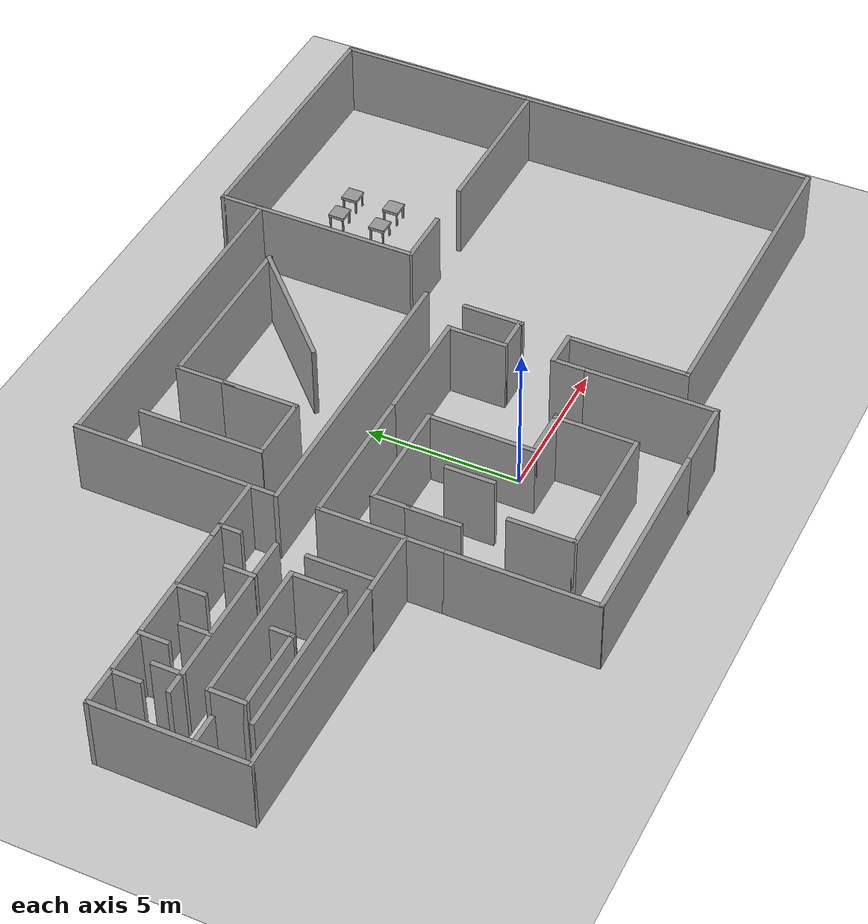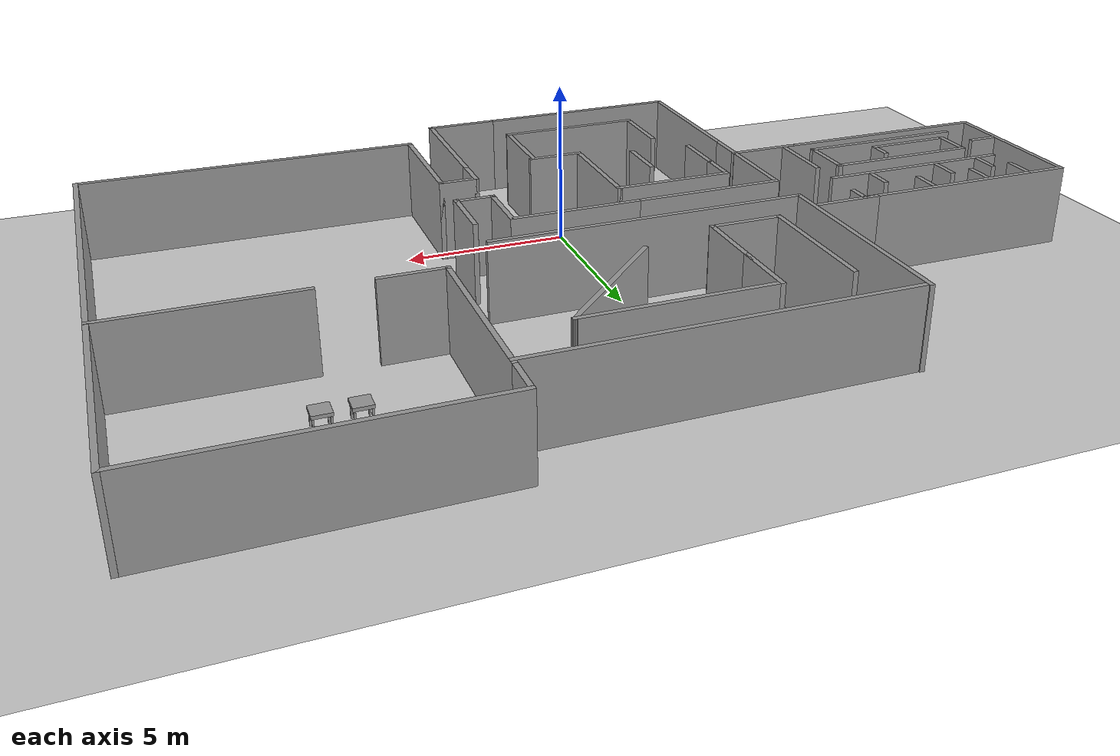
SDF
<sdf version="1.6">
 <world name="default">
  <light name="sun" type="directional">
   <pose>0 0 10 0 -0 0</pose>
   <diffuse>0.8 0.8 0.8 1</diffuse>
   <specular>0.1 0.1 0.1 1</specular>
   <attenuation>
    <range>1000</range>
    <constant>0.9</constant>
    <linear>0.01</linear>
    <quadratic>0.001</quadratic>
   </attenuation>
   <direction>-0.5 0.5 -1</direction>
  </light>
  <model name="ground_plane">
   <static>1</static>
   <link name="link">
    <collision name="collision">
     <geometry><plane><normal>0 0 1</normal><size>100 100</size></plane></geometry>
     <surface><friction><ode><mu>100</mu><mu2>50</mu2></ode></friction></surface>
    </collision>
    <visual name="visual">
     <cast_shadows>0</cast_shadows>
     <geometry><plane><normal>0 0 1</normal><size>100 100</size></plane></geometry>
     <material>
      <script><uri>file://media/materials/scripts/gazebo.material</uri><name>Gazebo/Grey</name></script>
     </material>
    </visual>
   </link>
  </model>
  <gravity>0 0 -9.8</gravity>
  <magnetic_field>6e-06 2.3e-05 -4.2e-05</magnetic_field>
  <atmosphere type="adiabatic"/>
  <physics name="default_physics" default="0" type="ode">
   <max_step_size>0.001</max_step_size>
   <real_time_factor>1</real_time_factor>
   <real_time_update_rate>1000</real_time_update_rate>
  </physics>
  <scene><ambient>0.4 0.4 0.4 1</ambient><background>0.7 0.7 0.7 1</background><shadows>1</shadows></scene>
  <spherical_coordinates>
   <surface_model>EARTH_WGS84</surface_model>
   <latitude_deg>0</latitude_deg>
   <longitude_deg>0</longitude_deg>
   <elevation>0</elevation>
   <heading_deg>0</heading_deg>
  </spherical_coordinates>
  <model name="Base1">
   <link name="Wall_11">
    <pose>-2.50761 -8.92183 0 0 -0 0</pose>
    <visual name="Wall_11_Visual">
     <pose>0 0 1.25 0 -0 0</pose>
     <geometry><box><size>2.25 0.15 2.5</size></box></geometry>
     <material>
      <script><uri>file://media/materials/scripts/gazebo.material</uri><name>Gazebo/Grey</name></script>
      <ambient>1 1 1 1</ambient>
      <diffuse>0.7 0.7 0.7 1</diffuse>
      <specular>0.01 0.01 0.01 1</specular>
      <emissive>0 0 0 1</emissive>
     </material>
    </visual>
    <collision name="Wall_11_Collision">
     <pose>0 0 1.25 0 -0 0</pose>
     <geometry><box><size>2.25 0.15 2.5</size></box></geometry>
     <surface>
      <friction>
       <ode><mu>1</mu><mu2>1</mu2><fdir1>0 0 0</fdir1><slip1>0</slip1><slip2>0</slip2></ode>
       <torsional>
        <coefficient>1</coefficient>
        <patch_radius>0</patch_radius>
        <surface_radius>0</surface_radius>
        <use_patch_radius>1</use_patch_radius>
        <ode><slip>0</slip></ode>
       </torsional>
      </friction>
      <bounce><restitution_coefficient>0</restitution_coefficient><threshold>1e+06</threshold></bounce>
      <contact>
       <collide_without_contact>0</collide_without_contact>
       <collide_without_contact_bitmask>1</collide_without_contact_bitmask>
       <collide_bitmask>1</collide_bitmask>
       <ode>
        <soft_cfm>0</soft_cfm>
        <soft_erp>0.2</soft_erp>
        <kp>1e+13</kp>
        <kd>1</kd>
        <max_vel>0.01</max_vel>
        <min_depth>0</min_depth>
       </ode>
       <bullet>
        <split_impulse>1</split_impulse>
        <split_impulse_penetration_threshold>-0.01</split_impulse_penetration_threshold>
        <soft_cfm>0</soft_cfm>
        <soft_erp>0.2</soft_erp>
        <kp>1e+13</kp>
        <kd>1</kd>
       </bullet>
      </contact>
     </surface>
    </collision>
   </link>
   <link name="Wall_12">
    <pose>-1.45761 -6.87183 0 0 -0 1.5708</pose>
    <visual name="Wall_12_Visual">
     <pose>0 0 1.25 0 -0 0</pose>
     <geometry><box><size>4.25 0.15 2.5</size></box></geometry>
     <material>
      <script><uri>file://media/materials/scripts/gazebo.material</uri><name>Gazebo/Grey</name></script>
      <ambient>1 1 1 1</ambient>
      <diffuse>0.7 0.7 0.7 1</diffuse>
      <specular>0.01 0.01 0.01 1</specular>
      <emissive>0 0 0 1</emissive>
     </material>
    </visual>
    <collision name="Wall_12_Collision">
     <pose>0 0 1.25 0 -0 0</pose>
     <geometry><box><size>4.25 0.15 2.5</size></box></geometry>
     <surface>
      <friction>
       <ode><mu>1</mu><mu2>1</mu2><fdir1>0 0 0</fdir1><slip1>0</slip1><slip2>0</slip2></ode>
       <torsional>
        <coefficient>1</coefficient>
        <patch_radius>0</patch_radius>
        <surface_radius>0</surface_radius>
        <use_patch_radius>1</use_patch_radius>
        <ode><slip>0</slip></ode>
       </torsional>
      </friction>
      <bounce><restitution_coefficient>0</restitution_coefficient><threshold>1e+06</threshold></bounce>
      <contact>
       <collide_without_contact>0</collide_without_contact>
       <collide_without_contact_bitmask>1</collide_without_contact_bitmask>
       <collide_bitmask>1</collide_bitmask>
       <ode>
        <soft_cfm>0</soft_cfm>
        <soft_erp>0.2</soft_erp>
        <kp>1e+13</kp>
        <kd>1</kd>
        <max_vel>0.01</max_vel>
        <min_depth>0</min_depth>
       </ode>
       <bullet>
        <split_impulse>1</split_impulse>
        <split_impulse_penetration_threshold>-0.01</split_impulse_penetration_threshold>
        <soft_cfm>0</soft_cfm>
        <soft_erp>0.2</soft_erp>
        <kp>1e+13</kp>
        <kd>1</kd>
       </bullet>
      </contact>
     </surface>
    </collision>
   </link>
   <link name="Wall_15">
    <pose>-8.84239 -3.32817 0 0 -0 1.5708</pose>
    <visual name="Wall_15_Visual">
     <pose>0 0 1.25 0 -0 0</pose>
     <geometry><box><size>1.75 0.15 2.5</size></box></geometry>
     <material>
      <script><uri>file://media/materials/scripts/gazebo.material</uri><name>Gazebo/Grey</name></script>
      <ambient>1 1 1 1</ambient>
      <diffuse>0.7 0.7 0.7 1</diffuse>
      <specular>0.01 0.01 0.01 1</specular>
      <emissive>0 0 0 1</emissive>
     </material>
    </visual>
    <collision name="Wall_15_Collision">
     <pose>0 0 1.25 0 -0 0</pose>
     <geometry><box><size>1.75 0.15 2.5</size></box></geometry>
     <surface>
      <friction>
       <ode><mu>1</mu><mu2>1</mu2><fdir1>0 0 0</fdir1><slip1>0</slip1><slip2>0</slip2></ode>
       <torsional>
        <coefficient>1</coefficient>
        <patch_radius>0</patch_radius>
        <surface_radius>0</surface_radius>
        <use_patch_radius>1</use_patch_radius>
        <ode><slip>0</slip></ode>
       </torsional>
      </friction>
      <bounce><restitution_coefficient>0</restitution_coefficient><threshold>1e+06</threshold></bounce>
      <contact>
       <collide_without_contact>0</collide_without_contact>
       <collide_without_contact_bitmask>1</collide_without_contact_bitmask>
       <collide_bitmask>1</collide_bitmask>
       <ode>
        <soft_cfm>0</soft_cfm>
        <soft_erp>0.2</soft_erp>
        <kp>1e+13</kp>
        <kd>1</kd>
        <max_vel>0.01</max_vel>
        <min_depth>0</min_depth>
       </ode>
       <bullet>
        <split_impulse>1</split_impulse>
        <split_impulse_penetration_threshold>-0.01</split_impulse_penetration_threshold>
        <soft_cfm>0</soft_cfm>
        <soft_erp>0.2</soft_erp>
        <kp>1e+13</kp>
        <kd>1</kd>
       </bullet>
      </contact>
     </surface>
    </collision>
   </link>
   <link name="Wall_16">
    <pose>-8.84239 -1.97817 0 0 -0 1.5708</pose>
    <visual name="Wall_16_Visual">
     <pose>0 0 1.25 0 -0 0</pose>
     <geometry><box><size>1.25 0.15 2.5</size></box></geometry>
     <material>
      <script><uri>file://media/materials/scripts/gazebo.material</uri><name>Gazebo/Grey</name></script>
      <ambient>1 1 1 1</ambient>
      <diffuse>0.7 0.7 0.7 1</diffuse>
      <specular>0.01 0.01 0.01 1</specular>
      <emissive>0 0 0 1</emissive>
     </material>
    </visual>
    <collision name="Wall_16_Collision">
     <pose>0 0 1.25 0 -0 0</pose>
     <geometry><box><size>1.25 0.15 2.5</size></box></geometry>
     <surface>
      <friction>
       <ode><mu>1</mu><mu2>1</mu2><fdir1>0 0 0</fdir1><slip1>0</slip1><slip2>0</slip2></ode>
       <torsional>
        <coefficient>1</coefficient>
        <patch_radius>0</patch_radius>
        <surface_radius>0</surface_radius>
        <use_patch_radius>1</use_patch_radius>
        <ode><slip>0</slip></ode>
       </torsional>
      </friction>
      <bounce><restitution_coefficient>0</restitution_coefficient><threshold>1e+06</threshold></bounce>
      <contact>
       <collide_without_contact>0</collide_without_contact>
       <collide_without_contact_bitmask>1</collide_without_contact_bitmask>
       <collide_bitmask>1</collide_bitmask>
       <ode>
        <soft_cfm>0</soft_cfm>
        <soft_erp>0.2</soft_erp>
        <kp>1e+13</kp>
        <kd>1</kd>
        <max_vel>0.01</max_vel>
        <min_depth>0</min_depth>
       </ode>
       <bullet>
        <split_impulse>1</split_impulse>
        <split_impulse_penetration_threshold>-0.01</split_impulse_penetration_threshold>
        <soft_cfm>0</soft_cfm>
        <soft_erp>0.2</soft_erp>
        <kp>1e+13</kp>
        <kd>1</kd>
       </bullet>
      </contact>
     </surface>
    </collision>
   </link>
   <link name="Wall_18">
    <pose>-9.94239 -2.20317 0 0 -0 1.5708</pose>
    <visual name="Wall_18_Visual">
     <pose>0 0 1.25 0 -0 0</pose>
     <geometry><box><size>4 0.15 2.5</size></box></geometry>
     <material>
      <script><uri>file://media/materials/scripts/gazebo.material</uri><name>Gazebo/Grey</name></script>
      <ambient>1 1 1 1</ambient>
      <diffuse>0.7 0.7 0.7 1</diffuse>
      <specular>0.01 0.01 0.01 1</specular>
      <emissive>0 0 0 1</emissive>
     </material>
    </visual>
    <collision name="Wall_18_Collision">
     <pose>0 0 1.25 0 -0 0</pose>
     <geometry><box><size>4 0.15 2.5</size></box></geometry>
     <surface>
      <friction>
       <ode><mu>1</mu><mu2>1</mu2><fdir1>0 0 0</fdir1><slip1>0</slip1><slip2>0</slip2></ode>
       <torsional>
        <coefficient>1</coefficient>
        <patch_radius>0</patch_radius>
        <surface_radius>0</surface_radius>
        <use_patch_radius>1</use_patch_radius>
        <ode><slip>0</slip></ode>
       </torsional>
      </friction>
      <bounce><restitution_coefficient>0</restitution_coefficient><threshold>1e+06</threshold></bounce>
      <contact>
       <collide_without_contact>0</collide_without_contact>
       <collide_without_contact_bitmask>1</collide_without_contact_bitmask>
       <collide_bitmask>1</collide_bitmask>
       <ode>
        <soft_cfm>0</soft_cfm>
        <soft_erp>0.2</soft_erp>
        <kp>1e+13</kp>
        <kd>1</kd>
        <max_vel>0.01</max_vel>
        <min_depth>0</min_depth>
       </ode>
       <bullet>
        <split_impulse>1</split_impulse>
        <split_impulse_penetration_threshold>-0.01</split_impulse_penetration_threshold>
        <soft_cfm>0</soft_cfm>
        <soft_erp>0.2</soft_erp>
        <kp>1e+13</kp>
        <kd>1</kd>
       </bullet>
      </contact>
     </surface>
    </collision>
   </link>
   <link name="Wall_20">
    <pose>-7.64239 -0.278166 0 0 -0 0</pose>
    <visual name="Wall_20_Visual">
     <pose>0 0 1.25 0 -0 0</pose>
     <geometry><box><size>4.75 0.15 2.5</size></box></geometry>
     <material>
      <script><uri>file://media/materials/scripts/gazebo.material</uri><name>Gazebo/Grey</name></script>
      <ambient>1 1 1 1</ambient>
      <diffuse>0.7 0.7 0.7 1</diffuse>
      <specular>0.01 0.01 0.01 1</specular>
      <emissive>0 0 0 1</emissive>
     </material>
    </visual>
    <collision name="Wall_20_Collision">
     <pose>0 0 1.25 0 -0 0</pose>
     <geometry><box><size>4.75 0.15 2.5</size></box></geometry>
     <surface>
      <friction>
       <ode><mu>1</mu><mu2>1</mu2><fdir1>0 0 0</fdir1><slip1>0</slip1><slip2>0</slip2></ode>
       <torsional>
        <coefficient>1</coefficient>
        <patch_radius>0</patch_radius>
        <surface_radius>0</surface_radius>
        <use_patch_radius>1</use_patch_radius>
        <ode><slip>0</slip></ode>
       </torsional>
      </friction>
      <bounce><restitution_coefficient>0</restitution_coefficient><threshold>1e+06</threshold></bounce>
      <contact>
       <collide_without_contact>0</collide_without_contact>
       <collide_without_contact_bitmask>1</collide_without_contact_bitmask>
       <collide_bitmask>1</collide_bitmask>
       <ode>
        <soft_cfm>0</soft_cfm>
        <soft_erp>0.2</soft_erp>
        <kp>1e+13</kp>
        <kd>1</kd>
        <max_vel>0.01</max_vel>
        <min_depth>0</min_depth>
       </ode>
       <bullet>
        <split_impulse>1</split_impulse>
        <split_impulse_penetration_threshold>-0.01</split_impulse_penetration_threshold>
        <soft_cfm>0</soft_cfm>
        <soft_erp>0.2</soft_erp>
        <kp>1e+13</kp>
        <kd>1</kd>
       </bullet>
      </contact>
     </surface>
    </collision>
   </link>
   <link name="Wall_22">
    <pose>-7.04239 -1.42817 0 0 -0 0</pose>
    <visual name="Wall_22_Visual">
     <pose>0 0 1.25 0 -0 0</pose>
     <geometry><box><size>3.75 0.15 2.5</size></box></geometry>
     <material>
      <script><uri>file://media/materials/scripts/gazebo.material</uri><name>Gazebo/Grey</name></script>
      <ambient>1 1 1 1</ambient>
      <diffuse>0.7 0.7 0.7 1</diffuse>
      <specular>0.01 0.01 0.01 1</specular>
      <emissive>0 0 0 1</emissive>
     </material>
    </visual>
    <collision name="Wall_22_Collision">
     <pose>0 0 1.25 0 -0 0</pose>
     <geometry><box><size>3.75 0.15 2.5</size></box></geometry>
     <surface>
      <friction>
       <ode><mu>1</mu><mu2>1</mu2><fdir1>0 0 0</fdir1><slip1>0</slip1><slip2>0</slip2></ode>
       <torsional>
        <coefficient>1</coefficient>
        <patch_radius>0</patch_radius>
        <surface_radius>0</surface_radius>
        <use_patch_radius>1</use_patch_radius>
        <ode><slip>0</slip></ode>
       </torsional>
      </friction>
      <bounce><restitution_coefficient>0</restitution_coefficient><threshold>1e+06</threshold></bounce>
      <contact>
       <collide_without_contact>0</collide_without_contact>
       <collide_without_contact_bitmask>1</collide_without_contact_bitmask>
       <collide_bitmask>1</collide_bitmask>
       <ode>
        <soft_cfm>0</soft_cfm>
        <soft_erp>0.2</soft_erp>
        <kp>1e+13</kp>
        <kd>1</kd>
        <max_vel>0.01</max_vel>
        <min_depth>0</min_depth>
       </ode>
       <bullet>
        <split_impulse>1</split_impulse>
        <split_impulse_penetration_threshold>-0.01</split_impulse_penetration_threshold>
        <soft_cfm>0</soft_cfm>
        <soft_erp>0.2</soft_erp>
        <kp>1e+13</kp>
        <kd>1</kd>
       </bullet>
      </contact>
     </surface>
    </collision>
   </link>
   <link name="Wall_27">
    <pose>-5.24239 -3.10317 0 0 0 -1.5708</pose>
    <visual name="Wall_27_Visual">
     <pose>0 0 1.25 0 -0 0</pose>
     <geometry><box><size>3.5 0.15 2.5</size></box></geometry>
     <material>
      <script><uri>file://media/materials/scripts/gazebo.material</uri><name>Gazebo/Grey</name></script>
      <ambient>1 1 1 1</ambient>
      <diffuse>0.7 0.7 0.7 1</diffuse>
      <specular>0.01 0.01 0.01 1</specular>
      <emissive>0 0 0 1</emissive>
     </material>
    </visual>
    <collision name="Wall_27_Collision">
     <pose>0 0 1.25 0 -0 0</pose>
     <geometry><box><size>3.5 0.15 2.5</size></box></geometry>
     <surface>
      <friction>
       <ode><mu>1</mu><mu2>1</mu2><fdir1>0 0 0</fdir1><slip1>0</slip1><slip2>0</slip2></ode>
       <torsional>
        <coefficient>1</coefficient>
        <patch_radius>0</patch_radius>
        <surface_radius>0</surface_radius>
        <use_patch_radius>1</use_patch_radius>
        <ode><slip>0</slip></ode>
       </torsional>
      </friction>
      <bounce><restitution_coefficient>0</restitution_coefficient><threshold>1e+06</threshold></bounce>
      <contact>
       <collide_without_contact>0</collide_without_contact>
       <collide_without_contact_bitmask>1</collide_without_contact_bitmask>
       <collide_bitmask>1</collide_bitmask>
       <ode>
        <soft_cfm>0</soft_cfm>
        <soft_erp>0.2</soft_erp>
        <kp>1e+13</kp>
        <kd>1</kd>
        <max_vel>0.01</max_vel>
        <min_depth>0</min_depth>
       </ode>
       <bullet>
        <split_impulse>1</split_impulse>
        <split_impulse_penetration_threshold>-0.01</split_impulse_penetration_threshold>
        <soft_cfm>0</soft_cfm>
        <soft_erp>0.2</soft_erp>
        <kp>1e+13</kp>
        <kd>1</kd>
       </bullet>
      </contact>
     </surface>
    </collision>
   </link>
   <link name="Wall_28">
    <pose>-4.44239 -4.77817 0 0 -0 0</pose>
    <visual name="Wall_28_Visual">
     <pose>0 0 1.25 0 -0 0</pose>
     <geometry><box><size>1.75 0.15 2.5</size></box></geometry>
     <material>
      <script><uri>file://media/materials/scripts/gazebo.material</uri><name>Gazebo/Grey</name></script>
      <ambient>1 1 1 1</ambient>
      <diffuse>0.7 0.7 0.7 1</diffuse>
      <specular>0.01 0.01 0.01 1</specular>
      <emissive>0 0 0 1</emissive>
     </material>
    </visual>
    <collision name="Wall_28_Collision">
     <pose>0 0 1.25 0 -0 0</pose>
     <geometry><box><size>1.75 0.15 2.5</size></box></geometry>
     <surface>
      <friction>
       <ode><mu>1</mu><mu2>1</mu2><fdir1>0 0 0</fdir1><slip1>0</slip1><slip2>0</slip2></ode>
       <torsional>
        <coefficient>1</coefficient>
        <patch_radius>0</patch_radius>
        <surface_radius>0</surface_radius>
        <use_patch_radius>1</use_patch_radius>
        <ode><slip>0</slip></ode>
       </torsional>
      </friction>
      <bounce><restitution_coefficient>0</restitution_coefficient><threshold>1e+06</threshold></bounce>
      <contact>
       <collide_without_contact>0</collide_without_contact>
       <collide_without_contact_bitmask>1</collide_without_contact_bitmask>
       <collide_bitmask>1</collide_bitmask>
       <ode>
        <soft_cfm>0</soft_cfm>
        <soft_erp>0.2</soft_erp>
        <kp>1e+13</kp>
        <kd>1</kd>
        <max_vel>0.01</max_vel>
        <min_depth>0</min_depth>
       </ode>
       <bullet>
        <split_impulse>1</split_impulse>
        <split_impulse_penetration_threshold>-0.01</split_impulse_penetration_threshold>
        <soft_cfm>0</soft_cfm>
        <soft_erp>0.2</soft_erp>
        <kp>1e+13</kp>
        <kd>1</kd>
       </bullet>
      </contact>
     </surface>
    </collision>
   </link>
   <link name="Wall_30">
    <pose>-1.45761 -4.27183 0 0 -0 1.5708</pose>
    <visual name="Wall_30_Visual">
     <pose>0 0 1.25 0 -0 0</pose>
     <geometry><box><size>1.25 0.15 2.5</size></box></geometry>
     <material>
      <script><uri>file://media/materials/scripts/gazebo.material</uri><name>Gazebo/Grey</name></script>
      <ambient>1 1 1 1</ambient>
      <diffuse>0.7 0.7 0.7 1</diffuse>
      <specular>0.01 0.01 0.01 1</specular>
      <emissive>0 0 0 1</emissive>
     </material>
    </visual>
    <collision name="Wall_30_Collision">
     <pose>0 0 1.25 0 -0 0</pose>
     <geometry><box><size>1.25 0.15 2.5</size></box></geometry>
     <surface>
      <friction>
       <ode><mu>1</mu><mu2>1</mu2><fdir1>0 0 0</fdir1><slip1>0</slip1><slip2>0</slip2></ode>
       <torsional>
        <coefficient>1</coefficient>
        <patch_radius>0</patch_radius>
        <surface_radius>0</surface_radius>
        <use_patch_radius>1</use_patch_radius>
        <ode><slip>0</slip></ode>
       </torsional>
      </friction>
      <bounce><restitution_coefficient>0</restitution_coefficient><threshold>1e+06</threshold></bounce>
      <contact>
       <collide_without_contact>0</collide_without_contact>
       <collide_without_contact_bitmask>1</collide_without_contact_bitmask>
       <collide_bitmask>1</collide_bitmask>
       <ode>
        <soft_cfm>0</soft_cfm>
        <soft_erp>0.2</soft_erp>
        <kp>1e+13</kp>
        <kd>1</kd>
        <max_vel>0.01</max_vel>
        <min_depth>0</min_depth>
       </ode>
       <bullet>
        <split_impulse>1</split_impulse>
        <split_impulse_penetration_threshold>-0.01</split_impulse_penetration_threshold>
        <soft_cfm>0</soft_cfm>
        <soft_erp>0.2</soft_erp>
        <kp>1e+13</kp>
        <kd>1</kd>
       </bullet>
      </contact>
     </surface>
    </collision>
   </link>
   <link name="Wall_35">
    <pose>-3.41739 -0.278166 0 0 -0 0</pose>
    <visual name="Wall_35_Visual">
     <pose>0 0 1.25 0 -0 0</pose>
     <geometry><box><size>4 0.15 2.5</size></box></geometry>
     <material>
      <script><uri>file://media/materials/scripts/gazebo.material</uri><name>Gazebo/Grey</name></script>
      <ambient>1 1 1 1</ambient>
      <diffuse>0.7 0.7 0.7 1</diffuse>
      <specular>0.01 0.01 0.01 1</specular>
      <emissive>0 0 0 1</emissive>
     </material>
    </visual>
    <collision name="Wall_35_Collision">
     <pose>0 0 1.25 0 -0 0</pose>
     <geometry><box><size>4 0.15 2.5</size></box></geometry>
     <surface>
      <friction>
       <ode><mu>1</mu><mu2>1</mu2><fdir1>0 0 0</fdir1><slip1>0</slip1><slip2>0</slip2></ode>
       <torsional>
        <coefficient>1</coefficient>
        <patch_radius>0</patch_radius>
        <surface_radius>0</surface_radius>
        <use_patch_radius>1</use_patch_radius>
        <ode><slip>0</slip></ode>
       </torsional>
      </friction>
      <bounce><restitution_coefficient>0</restitution_coefficient><threshold>1e+06</threshold></bounce>
      <contact>
       <collide_without_contact>0</collide_without_contact>
       <collide_without_contact_bitmask>1</collide_without_contact_bitmask>
       <collide_bitmask>1</collide_bitmask>
       <ode>
        <soft_cfm>0</soft_cfm>
        <soft_erp>0.2</soft_erp>
        <kp>1e+13</kp>
        <kd>1</kd>
        <max_vel>0.01</max_vel>
        <min_depth>0</min_depth>
       </ode>
       <bullet>
        <split_impulse>1</split_impulse>
        <split_impulse_penetration_threshold>-0.01</split_impulse_penetration_threshold>
        <soft_cfm>0</soft_cfm>
        <soft_erp>0.2</soft_erp>
        <kp>1e+13</kp>
        <kd>1</kd>
       </bullet>
      </contact>
     </surface>
    </collision>
   </link>
   <link name="Wall_36">
    <pose>-1.49239 -1.20317 0 0 0 -1.5708</pose>
    <visual name="Wall_36_Visual">
     <pose>0 0 1.25 0 -0 0</pose>
     <geometry><box><size>2 0.15 2.5</size></box></geometry>
     <material>
      <script><uri>file://media/materials/scripts/gazebo.material</uri><name>Gazebo/Grey</name></script>
      <ambient>1 1 1 1</ambient>
      <diffuse>0.7 0.7 0.7 1</diffuse>
      <specular>0.01 0.01 0.01 1</specular>
      <emissive>0 0 0 1</emissive>
     </material>
    </visual>
    <collision name="Wall_36_Collision">
     <pose>0 0 1.25 0 -0 0</pose>
     <geometry><box><size>2 0.15 2.5</size></box></geometry>
     <surface>
      <friction>
       <ode><mu>1</mu><mu2>1</mu2><fdir1>0 0 0</fdir1><slip1>0</slip1><slip2>0</slip2></ode>
       <torsional>
        <coefficient>1</coefficient>
        <patch_radius>0</patch_radius>
        <surface_radius>0</surface_radius>
        <use_patch_radius>1</use_patch_radius>
        <ode><slip>0</slip></ode>
       </torsional>
      </friction>
      <bounce><restitution_coefficient>0</restitution_coefficient><threshold>1e+06</threshold></bounce>
      <contact>
       <collide_without_contact>0</collide_without_contact>
       <collide_without_contact_bitmask>1</collide_without_contact_bitmask>
       <collide_bitmask>1</collide_bitmask>
       <ode>
        <soft_cfm>0</soft_cfm>
        <soft_erp>0.2</soft_erp>
        <kp>1e+13</kp>
        <kd>1</kd>
        <max_vel>0.01</max_vel>
        <min_depth>0</min_depth>
       </ode>
       <bullet>
        <split_impulse>1</split_impulse>
        <split_impulse_penetration_threshold>-0.01</split_impulse_penetration_threshold>
        <soft_cfm>0</soft_cfm>
        <soft_erp>0.2</soft_erp>
        <kp>1e+13</kp>
        <kd>1</kd>
       </bullet>
      </contact>
     </surface>
    </collision>
   </link>
   <link name="Wall_37">
    <pose>-0.94239 -2.12817 0 0 -0 0</pose>
    <visual name="Wall_37_Visual">
     <pose>0 0 1.25 0 -0 0</pose>
     <geometry><box><size>1.25 0.15 2.5</size></box></geometry>
     <material>
      <script><uri>file://media/materials/scripts/gazebo.material</uri><name>Gazebo/Grey</name></script>
      <ambient>1 1 1 1</ambient>
      <diffuse>0.7 0.7 0.7 1</diffuse>
      <specular>0.01 0.01 0.01 1</specular>
      <emissive>0 0 0 1</emissive>
     </material>
    </visual>
    <collision name="Wall_37_Collision">
     <pose>0 0 1.25 0 -0 0</pose>
     <geometry><box><size>1.25 0.15 2.5</size></box></geometry>
     <surface>
      <friction>
       <ode><mu>1</mu><mu2>1</mu2><fdir1>0 0 0</fdir1><slip1>0</slip1><slip2>0</slip2></ode>
       <torsional>
        <coefficient>1</coefficient>
        <patch_radius>0</patch_radius>
        <surface_radius>0</surface_radius>
        <use_patch_radius>1</use_patch_radius>
        <ode><slip>0</slip></ode>
       </torsional>
      </friction>
      <bounce><restitution_coefficient>0</restitution_coefficient><threshold>1e+06</threshold></bounce>
      <contact>
       <collide_without_contact>0</collide_without_contact>
       <collide_without_contact_bitmask>1</collide_without_contact_bitmask>
       <collide_bitmask>1</collide_bitmask>
       <ode>
        <soft_cfm>0</soft_cfm>
        <soft_erp>0.2</soft_erp>
        <kp>1e+13</kp>
        <kd>1</kd>
        <max_vel>0.01</max_vel>
        <min_depth>0</min_depth>
       </ode>
       <bullet>
        <split_impulse>1</split_impulse>
        <split_impulse_penetration_threshold>-0.01</split_impulse_penetration_threshold>
        <soft_cfm>0</soft_cfm>
        <soft_erp>0.2</soft_erp>
        <kp>1e+13</kp>
        <kd>1</kd>
       </bullet>
      </contact>
     </surface>
    </collision>
   </link>
   <link name="Wall_39">
    <pose>-0.90761 -3.72183 0 0 -0 0</pose>
    <visual name="Wall_39_Visual">
     <pose>0 0 1.25 0 -0 0</pose>
     <geometry><box><size>1.25 0.15 2.5</size></box></geometry>
     <material>
      <script><uri>file://media/materials/scripts/gazebo.material</uri><name>Gazebo/Grey</name></script>
      <ambient>1 1 1 1</ambient>
      <diffuse>0.7 0.7 0.7 1</diffuse>
      <specular>0.01 0.01 0.01 1</specular>
      <emissive>0 0 0 1</emissive>
     </material>
    </visual>
    <collision name="Wall_39_Collision">
     <pose>0 0 1.25 0 -0 0</pose>
     <geometry><box><size>1.25 0.15 2.5</size></box></geometry>
     <surface>
      <friction>
       <ode><mu>1</mu><mu2>1</mu2><fdir1>0 0 0</fdir1><slip1>0</slip1><slip2>0</slip2></ode>
       <torsional>
        <coefficient>1</coefficient>
        <patch_radius>0</patch_radius>
        <surface_radius>0</surface_radius>
        <use_patch_radius>1</use_patch_radius>
        <ode><slip>0</slip></ode>
       </torsional>
      </friction>
      <bounce><restitution_coefficient>0</restitution_coefficient><threshold>1e+06</threshold></bounce>
      <contact>
       <collide_without_contact>0</collide_without_contact>
       <collide_without_contact_bitmask>1</collide_without_contact_bitmask>
       <collide_bitmask>1</collide_bitmask>
       <ode>
        <soft_cfm>0</soft_cfm>
        <soft_erp>0.2</soft_erp>
        <kp>1e+13</kp>
        <kd>1</kd>
        <max_vel>0.01</max_vel>
        <min_depth>0</min_depth>
       </ode>
       <bullet>
        <split_impulse>1</split_impulse>
        <split_impulse_penetration_threshold>-0.01</split_impulse_penetration_threshold>
        <soft_cfm>0</soft_cfm>
        <soft_erp>0.2</soft_erp>
        <kp>1e+13</kp>
        <kd>1</kd>
       </bullet>
      </contact>
     </surface>
    </collision>
   </link>
   <link name="Wall_4">
    <pose>-9.94239 -6.55926 0 0 0 -1.5708</pose>
    <inertial>
     <inertia><ixx>nan</ixx><ixy>0</ixy><ixz>0</ixz><iyy>nan</iyy><iyz>0</iyz><izz>nan</izz></inertia>
     <mass>0</mass>
    </inertial>
    <visual name="Wall_4_Visual">
     <pose>0 0 1.25 0 -0 0</pose>
     <geometry><box><size>4.84531 0.15 2.5</size></box></geometry>
     <material>
      <script><uri>file://media/materials/scripts/gazebo.material</uri><name>Gazebo/Grey</name></script>
      <ambient>1 1 1 1</ambient>
      <diffuse>0.7 0.7 0.7 1</diffuse>
      <specular>0.01 0.01 0.01 1</specular>
      <emissive>0 0 0 1</emissive>
     </material>
    </visual>
    <collision name="Wall_4_Collision">
     <pose>0 0 1.25 0 -0 0</pose>
     <geometry><box><size>4.84531 0.15 2.5</size></box></geometry>
     <surface>
      <friction>
       <ode><mu>1</mu><mu2>1</mu2><fdir1>0 0 0</fdir1><slip1>0</slip1><slip2>0</slip2></ode>
       <torsional>
        <coefficient>1</coefficient>
        <patch_radius>0</patch_radius>
        <surface_radius>0</surface_radius>
        <use_patch_radius>1</use_patch_radius>
        <ode><slip>0</slip></ode>
       </torsional>
      </friction>
      <bounce><restitution_coefficient>0</restitution_coefficient><threshold>1e+06</threshold></bounce>
      <contact>
       <collide_without_contact>0</collide_without_contact>
       <collide_without_contact_bitmask>1</collide_without_contact_bitmask>
       <collide_bitmask>1</collide_bitmask>
       <ode>
        <soft_cfm>0</soft_cfm>
        <soft_erp>0.2</soft_erp>
        <kp>1e+13</kp>
        <kd>1</kd>
        <max_vel>0.01</max_vel>
        <min_depth>0</min_depth>
       </ode>
       <bullet>
        <split_impulse>1</split_impulse>
        <split_impulse_penetration_threshold>-0.01</split_impulse_penetration_threshold>
        <soft_cfm>0</soft_cfm>
        <soft_erp>0.2</soft_erp>
        <kp>1e+13</kp>
        <kd>1</kd>
       </bullet>
      </contact>
     </surface>
    </collision>
   </link>
   <link name="Wall_40">
    <pose>-0.357611 -5.64683 0 0 0 -1.5708</pose>
    <visual name="Wall_40_Visual">
     <pose>0 0 1.25 0 -0 0</pose>
     <geometry><box><size>4 0.15 2.5</size></box></geometry>
     <material>
      <script><uri>file://media/materials/scripts/gazebo.material</uri><name>Gazebo/Grey</name></script>
      <ambient>1 1 1 1</ambient>
      <diffuse>0.7 0.7 0.7 1</diffuse>
      <specular>0.01 0.01 0.01 1</specular>
      <emissive>0 0 0 1</emissive>
     </material>
    </visual>
    <collision name="Wall_40_Collision">
     <pose>0 0 1.25 0 -0 0</pose>
     <geometry><box><size>4 0.15 2.5</size></box></geometry>
     <surface>
      <friction>
       <ode><mu>1</mu><mu2>1</mu2><fdir1>0 0 0</fdir1><slip1>0</slip1><slip2>0</slip2></ode>
       <torsional>
        <coefficient>1</coefficient>
        <patch_radius>0</patch_radius>
        <surface_radius>0</surface_radius>
        <use_patch_radius>1</use_patch_radius>
        <ode><slip>0</slip></ode>
       </torsional>
      </friction>
      <bounce><restitution_coefficient>0</restitution_coefficient><threshold>1e+06</threshold></bounce>
      <contact>
       <collide_without_contact>0</collide_without_contact>
       <collide_without_contact_bitmask>1</collide_without_contact_bitmask>
       <collide_bitmask>1</collide_bitmask>
       <ode>
        <soft_cfm>0</soft_cfm>
        <soft_erp>0.2</soft_erp>
        <kp>1e+13</kp>
        <kd>1</kd>
        <max_vel>0.01</max_vel>
        <min_depth>0</min_depth>
       </ode>
       <bullet>
        <split_impulse>1</split_impulse>
        <split_impulse_penetration_threshold>-0.01</split_impulse_penetration_threshold>
        <soft_cfm>0</soft_cfm>
        <soft_erp>0.2</soft_erp>
        <kp>1e+13</kp>
        <kd>1</kd>
       </bullet>
      </contact>
     </surface>
    </collision>
   </link>
   <link name="Wall_42">
    <pose>4.81739 -7.57183 0 0 -0 0</pose>
    <visual name="Wall_42_Visual">
     <pose>0 0 1.25 0 -0 0</pose>
     <geometry><box><size>10.5 0.15 2.5</size></box></geometry>
     <material>
      <script><uri>file://media/materials/scripts/gazebo.material</uri><name>Gazebo/Grey</name></script>
      <ambient>1 1 1 1</ambient>
      <diffuse>0.7 0.7 0.7 1</diffuse>
      <specular>0.01 0.01 0.01 1</specular>
      <emissive>0 0 0 1</emissive>
     </material>
    </visual>
    <collision name="Wall_42_Collision">
     <pose>0 0 1.25 0 -0 0</pose>
     <geometry><box><size>10.5 0.15 2.5</size></box></geometry>
     <surface>
      <friction>
       <ode><mu>1</mu><mu2>1</mu2><fdir1>0 0 0</fdir1><slip1>0</slip1><slip2>0</slip2></ode>
       <torsional>
        <coefficient>1</coefficient>
        <patch_radius>0</patch_radius>
        <surface_radius>0</surface_radius>
        <use_patch_radius>1</use_patch_radius>
        <ode><slip>0</slip></ode>
       </torsional>
      </friction>
      <bounce><restitution_coefficient>0</restitution_coefficient><threshold>1e+06</threshold></bounce>
      <contact>
       <collide_without_contact>0</collide_without_contact>
       <collide_without_contact_bitmask>1</collide_without_contact_bitmask>
       <collide_bitmask>1</collide_bitmask>
       <ode>
        <soft_cfm>0</soft_cfm>
        <soft_erp>0.2</soft_erp>
        <kp>1e+13</kp>
        <kd>1</kd>
        <max_vel>0.01</max_vel>
        <min_depth>0</min_depth>
       </ode>
       <bullet>
        <split_impulse>1</split_impulse>
        <split_impulse_penetration_threshold>-0.01</split_impulse_penetration_threshold>
        <soft_cfm>0</soft_cfm>
        <soft_erp>0.2</soft_erp>
        <kp>1e+13</kp>
        <kd>1</kd>
       </bullet>
      </contact>
     </surface>
    </collision>
   </link>
   <link name="Wall_43">
    <pose>9.99239 -2.64683 0 0 -0 1.5708</pose>
    <visual name="Wall_43_Visual">
     <pose>0 0 1.25 0 -0 0</pose>
     <geometry><box><size>10 0.15 2.5</size></box></geometry>
     <material>
      <script><uri>file://media/materials/scripts/gazebo.material</uri><name>Gazebo/Grey</name></script>
      <ambient>1 1 1 1</ambient>
      <diffuse>0.7 0.7 0.7 1</diffuse>
      <specular>0.01 0.01 0.01 1</specular>
      <emissive>0 0 0 1</emissive>
     </material>
    </visual>
    <collision name="Wall_43_Collision">
     <pose>0 0 1.25 0 -0 0</pose>
     <geometry><box><size>10 0.15 2.5</size></box></geometry>
     <surface>
      <friction>
       <ode><mu>1</mu><mu2>1</mu2><fdir1>0 0 0</fdir1><slip1>0</slip1><slip2>0</slip2></ode>
       <torsional>
        <coefficient>1</coefficient>
        <patch_radius>0</patch_radius>
        <surface_radius>0</surface_radius>
        <use_patch_radius>1</use_patch_radius>
        <ode><slip>0</slip></ode>
       </torsional>
      </friction>
      <bounce><restitution_coefficient>0</restitution_coefficient><threshold>1e+06</threshold></bounce>
      <contact>
       <collide_without_contact>0</collide_without_contact>
       <collide_without_contact_bitmask>1</collide_without_contact_bitmask>
       <collide_bitmask>1</collide_bitmask>
       <ode>
        <soft_cfm>0</soft_cfm>
        <soft_erp>0.2</soft_erp>
        <kp>1e+13</kp>
        <kd>1</kd>
        <max_vel>0.01</max_vel>
        <min_depth>0</min_depth>
       </ode>
       <bullet>
        <split_impulse>1</split_impulse>
        <split_impulse_penetration_threshold>-0.01</split_impulse_penetration_threshold>
        <soft_cfm>0</soft_cfm>
        <soft_erp>0.2</soft_erp>
        <kp>1e+13</kp>
        <kd>1</kd>
       </bullet>
      </contact>
     </surface>
    </collision>
   </link>
   <link name="Wall_44">
    <pose>7.31739 2.27817 0 0 -0 3.14159</pose>
    <visual name="Wall_44_Visual">
     <pose>0 0 1.25 0 -0 0</pose>
     <geometry><box><size>5.5 0.15 2.5</size></box></geometry>
     <material>
      <script><uri>file://media/materials/scripts/gazebo.material</uri><name>Gazebo/Grey</name></script>
      <ambient>1 1 1 1</ambient>
      <diffuse>0.7 0.7 0.7 1</diffuse>
      <specular>0.01 0.01 0.01 1</specular>
      <emissive>0 0 0 1</emissive>
     </material>
    </visual>
    <collision name="Wall_44_Collision">
     <pose>0 0 1.25 0 -0 0</pose>
     <geometry><box><size>5.5 0.15 2.5</size></box></geometry>
     <surface>
      <friction>
       <ode><mu>1</mu><mu2>1</mu2><fdir1>0 0 0</fdir1><slip1>0</slip1><slip2>0</slip2></ode>
       <torsional>
        <coefficient>1</coefficient>
        <patch_radius>0</patch_radius>
        <surface_radius>0</surface_radius>
        <use_patch_radius>1</use_patch_radius>
        <ode><slip>0</slip></ode>
       </torsional>
      </friction>
      <bounce><restitution_coefficient>0</restitution_coefficient><threshold>1e+06</threshold></bounce>
      <contact>
       <collide_without_contact>0</collide_without_contact>
       <collide_without_contact_bitmask>1</collide_without_contact_bitmask>
       <collide_bitmask>1</collide_bitmask>
       <ode>
        <soft_cfm>0</soft_cfm>
        <soft_erp>0.2</soft_erp>
        <kp>1e+13</kp>
        <kd>1</kd>
        <max_vel>0.01</max_vel>
        <min_depth>0</min_depth>
       </ode>
       <bullet>
        <split_impulse>1</split_impulse>
        <split_impulse_penetration_threshold>-0.01</split_impulse_penetration_threshold>
        <soft_cfm>0</soft_cfm>
        <soft_erp>0.2</soft_erp>
        <kp>1e+13</kp>
        <kd>1</kd>
       </bullet>
      </contact>
     </surface>
    </collision>
   </link>
   <link name="Wall_46">
    <pose>-0.392388 -1.23954 0 0 -0 1.5708</pose>
    <inertial>
     <inertia><ixx>nan</ixx><ixy>0</ixy><ixz>0</ixz><iyy>nan</iyy><iyz>0</iyz><izz>nan</izz></inertia>
     <mass>0</mass>
    </inertial>
    <visual name="Wall_46_Visual">
     <pose>0 0 1.25 0 -0 0</pose>
     <geometry><box><size>2.01222 0.15 2.5</size></box></geometry>
     <material>
      <script><uri>file://media/materials/scripts/gazebo.material</uri><name>Gazebo/Grey</name></script>
      <ambient>1 1 1 1</ambient>
      <diffuse>0.7 0.7 0.7 1</diffuse>
      <specular>0.01 0.01 0.01 1</specular>
      <emissive>0 0 0 1</emissive>
     </material>
    </visual>
    <collision name="Wall_46_Collision">
     <pose>0 0 1.25 0 -0 0</pose>
     <geometry><box><size>2.01222 0.15 2.5</size></box></geometry>
     <surface>
      <friction>
       <ode><mu>1</mu><mu2>1</mu2><fdir1>0 0 0</fdir1><slip1>0</slip1><slip2>0</slip2></ode>
       <torsional>
        <coefficient>1</coefficient>
        <patch_radius>0</patch_radius>
        <surface_radius>0</surface_radius>
        <use_patch_radius>1</use_patch_radius>
        <ode><slip>0</slip></ode>
       </torsional>
      </friction>
      <bounce><restitution_coefficient>0</restitution_coefficient><threshold>1e+06</threshold></bounce>
      <contact>
       <collide_without_contact>0</collide_without_contact>
       <collide_without_contact_bitmask>1</collide_without_contact_bitmask>
       <collide_bitmask>1</collide_bitmask>
       <ode>
        <soft_cfm>0</soft_cfm>
        <soft_erp>0.2</soft_erp>
        <kp>1e+13</kp>
        <kd>1</kd>
        <max_vel>0.01</max_vel>
        <min_depth>0</min_depth>
       </ode>
       <bullet>
        <split_impulse>1</split_impulse>
        <split_impulse_penetration_threshold>-0.01</split_impulse_penetration_threshold>
        <soft_cfm>0</soft_cfm>
        <soft_erp>0.2</soft_erp>
        <kp>1e+13</kp>
        <kd>1</kd>
       </bullet>
      </contact>
     </surface>
    </collision>
   </link>
   <link name="Wall_5">
    <pose>-6.73261 -8.92183 0 0 -0 0</pose>
    <visual name="Wall_5_Visual">
     <pose>0 0 1.25 0 -0 0</pose>
     <geometry><box><size>6.5 0.15 2.5</size></box></geometry>
     <material>
      <script><uri>file://media/materials/scripts/gazebo.material</uri><name>Gazebo/Grey</name></script>
      <ambient>1 1 1 1</ambient>
      <diffuse>0.7 0.7 0.7 1</diffuse>
      <specular>0.01 0.01 0.01 1</specular>
      <emissive>0 0 0 1</emissive>
     </material>
    </visual>
    <collision name="Wall_5_Collision">
     <pose>0 0 1.25 0 -0 0</pose>
     <geometry><box><size>6.5 0.15 2.5</size></box></geometry>
     <surface>
      <friction>
       <ode><mu>1</mu><mu2>1</mu2><fdir1>0 0 0</fdir1><slip1>0</slip1><slip2>0</slip2></ode>
       <torsional>
        <coefficient>1</coefficient>
        <patch_radius>0</patch_radius>
        <surface_radius>0</surface_radius>
        <use_patch_radius>1</use_patch_radius>
        <ode><slip>0</slip></ode>
       </torsional>
      </friction>
      <bounce><restitution_coefficient>0</restitution_coefficient><threshold>1e+06</threshold></bounce>
      <contact>
       <collide_without_contact>0</collide_without_contact>
       <collide_without_contact_bitmask>1</collide_without_contact_bitmask>
       <collide_bitmask>1</collide_bitmask>
       <ode>
        <soft_cfm>0</soft_cfm>
        <soft_erp>0.2</soft_erp>
        <kp>1e+13</kp>
        <kd>1</kd>
        <max_vel>0.01</max_vel>
        <min_depth>0</min_depth>
       </ode>
       <bullet>
        <split_impulse>1</split_impulse>
        <split_impulse_penetration_threshold>-0.01</split_impulse_penetration_threshold>
        <soft_cfm>0</soft_cfm>
        <soft_erp>0.2</soft_erp>
        <kp>1e+13</kp>
        <kd>1</kd>
       </bullet>
      </contact>
     </surface>
    </collision>
   </link>
   <link name="Wall_51">
    <pose>-5.19239 1.02858 0 0 -0 3.14159</pose>
    <visual name="Wall_51_Visual">
     <pose>0 0 1.25 0 -0 0</pose>
     <geometry><box><size>9.75 0.15 2.5</size></box></geometry>
     <material>
      <script><uri>file://media/materials/scripts/gazebo.material</uri><name>Gazebo/Grey</name></script>
      <ambient>1 1 1 1</ambient>
      <diffuse>0.7 0.7 0.7 1</diffuse>
      <specular>0.01 0.01 0.01 1</specular>
      <emissive>0 0 0 1</emissive>
     </material>
    </visual>
    <collision name="Wall_51_Collision">
     <pose>0 0 1.25 0 -0 0</pose>
     <geometry><box><size>9.75 0.15 2.5</size></box></geometry>
     <surface>
      <friction>
       <ode><mu>1</mu><mu2>1</mu2><fdir1>0 0 0</fdir1><slip1>0</slip1><slip2>0</slip2></ode>
       <torsional>
        <coefficient>1</coefficient>
        <patch_radius>0</patch_radius>
        <surface_radius>0</surface_radius>
        <use_patch_radius>1</use_patch_radius>
        <ode><slip>0</slip></ode>
       </torsional>
      </friction>
      <bounce><restitution_coefficient>0</restitution_coefficient><threshold>1e+06</threshold></bounce>
      <contact>
       <collide_without_contact>0</collide_without_contact>
       <collide_without_contact_bitmask>1</collide_without_contact_bitmask>
       <collide_bitmask>1</collide_bitmask>
       <ode>
        <soft_cfm>0</soft_cfm>
        <soft_erp>0.2</soft_erp>
        <kp>1e+13</kp>
        <kd>1</kd>
        <max_vel>0.01</max_vel>
        <min_depth>0</min_depth>
       </ode>
       <bullet>
        <split_impulse>1</split_impulse>
        <split_impulse_penetration_threshold>-0.01</split_impulse_penetration_threshold>
        <soft_cfm>0</soft_cfm>
        <soft_erp>0.2</soft_erp>
        <kp>1e+13</kp>
        <kd>1</kd>
       </bullet>
      </contact>
     </surface>
    </collision>
   </link>
   <link name="Wall_52">
    <pose>-9.99239 4.3211 0 0 -0 1.5708</pose>
    <inertial>
     <inertia><ixx>nan</ixx><ixy>0</ixy><ixz>0</ixz><iyy>nan</iyy><iyz>0</iyz><izz>nan</izz></inertia>
     <mass>0</mass>
    </inertial>
    <visual name="Wall_52_Visual">
     <pose>0 0 1.25 0 -0 0</pose>
     <geometry><box><size>6.71297 0.15 2.5</size></box></geometry>
     <material>
      <script><uri>file://media/materials/scripts/gazebo.material</uri><name>Gazebo/Grey</name></script>
      <ambient>1 1 1 1</ambient>
      <diffuse>0.7 0.7 0.7 1</diffuse>
      <specular>0.01 0.01 0.01 1</specular>
      <emissive>0 0 0 1</emissive>
     </material>
    </visual>
    <collision name="Wall_52_Collision">
     <pose>0 0 1.25 0 -0 0</pose>
     <geometry><box><size>6.71297 0.15 2.5</size></box></geometry>
     <surface>
      <friction>
       <ode><mu>1</mu><mu2>1</mu2><fdir1>0 0 0</fdir1><slip1>0</slip1><slip2>0</slip2></ode>
       <torsional>
        <coefficient>1</coefficient>
        <patch_radius>0</patch_radius>
        <surface_radius>0</surface_radius>
        <use_patch_radius>1</use_patch_radius>
        <ode><slip>0</slip></ode>
       </torsional>
      </friction>
      <bounce><restitution_coefficient>0</restitution_coefficient><threshold>1e+06</threshold></bounce>
      <contact>
       <collide_without_contact>0</collide_without_contact>
       <collide_without_contact_bitmask>1</collide_without_contact_bitmask>
       <collide_bitmask>1</collide_bitmask>
       <ode>
        <soft_cfm>0</soft_cfm>
        <soft_erp>0.2</soft_erp>
        <kp>1e+13</kp>
        <kd>1</kd>
        <max_vel>0.01</max_vel>
        <min_depth>0</min_depth>
       </ode>
       <bullet>
        <split_impulse>1</split_impulse>
        <split_impulse_penetration_threshold>-0.01</split_impulse_penetration_threshold>
        <soft_cfm>0</soft_cfm>
        <soft_erp>0.2</soft_erp>
        <kp>1e+13</kp>
        <kd>1</kd>
       </bullet>
      </contact>
     </surface>
    </collision>
   </link>
   <link name="Wall_53">
    <pose>-4.44239 7.57183 0 0 -0 0</pose>
    <visual name="Wall_53_Visual">
     <pose>0 0 1.25 0 -0 0</pose>
     <geometry><box><size>11.25 0.15 2.5</size></box></geometry>
     <material>
      <script><uri>file://media/materials/scripts/gazebo.material</uri><name>Gazebo/Grey</name></script>
      <ambient>1 1 1 1</ambient>
      <diffuse>0.7 0.7 0.7 1</diffuse>
      <specular>0.01 0.01 0.01 1</specular>
      <emissive>0 0 0 1</emissive>
     </material>
    </visual>
    <collision name="Wall_53_Collision">
     <pose>0 0 1.25 0 -0 0</pose>
     <geometry><box><size>11.25 0.15 2.5</size></box></geometry>
     <surface>
      <friction>
       <ode><mu>1</mu><mu2>1</mu2><fdir1>0 0 0</fdir1><slip1>0</slip1><slip2>0</slip2></ode>
       <torsional>
        <coefficient>1</coefficient>
        <patch_radius>0</patch_radius>
        <surface_radius>0</surface_radius>
        <use_patch_radius>1</use_patch_radius>
        <ode><slip>0</slip></ode>
       </torsional>
      </friction>
      <bounce><restitution_coefficient>0</restitution_coefficient><threshold>1e+06</threshold></bounce>
      <contact>
       <collide_without_contact>0</collide_without_contact>
       <collide_without_contact_bitmask>1</collide_without_contact_bitmask>
       <collide_bitmask>1</collide_bitmask>
       <ode>
        <soft_cfm>0</soft_cfm>
        <soft_erp>0.2</soft_erp>
        <kp>1e+13</kp>
        <kd>1</kd>
        <max_vel>0.01</max_vel>
        <min_depth>0</min_depth>
       </ode>
       <bullet>
        <split_impulse>1</split_impulse>
        <split_impulse_penetration_threshold>-0.01</split_impulse_penetration_threshold>
        <soft_cfm>0</soft_cfm>
        <soft_erp>0.2</soft_erp>
        <kp>1e+13</kp>
        <kd>1</kd>
       </bullet>
      </contact>
     </surface>
    </collision>
   </link>
   <link name="Wall_54">
    <pose>1.10761 5.02183 0 0 0 -1.5708</pose>
    <inertial>
     <inertia><ixx>nan</ixx><ixy>0</ixy><ixz>0</ixz><iyy>nan</iyy><iyz>0</iyz><izz>nan</izz></inertia>
     <mass>0</mass>
    </inertial>
    <visual name="Wall_54_Visual">
     <pose>0 0 1.25 0 -0 0</pose>
     <geometry><box><size>5.47385 0.15 2.5</size></box></geometry>
     <material>
      <script><uri>file://media/materials/scripts/gazebo.material</uri><name>Gazebo/Grey</name></script>
      <ambient>1 1 1 1</ambient>
      <diffuse>0.7 0.7 0.7 1</diffuse>
      <specular>0.01 0.01 0.01 1</specular>
      <emissive>0 0 0 1</emissive>
     </material>
    </visual>
    <collision name="Wall_54_Collision">
     <pose>0 0 1.25 0 -0 0</pose>
     <geometry><box><size>5.47385 0.15 2.5</size></box></geometry>
     <surface>
      <friction>
       <ode><mu>1</mu><mu2>1</mu2><fdir1>0 0 0</fdir1><slip1>0</slip1><slip2>0</slip2></ode>
       <torsional>
        <coefficient>1</coefficient>
        <patch_radius>0</patch_radius>
        <surface_radius>0</surface_radius>
        <use_patch_radius>1</use_patch_radius>
        <ode><slip>0</slip></ode>
       </torsional>
      </friction>
      <bounce><restitution_coefficient>0</restitution_coefficient><threshold>1e+06</threshold></bounce>
      <contact>
       <collide_without_contact>0</collide_without_contact>
       <collide_without_contact_bitmask>1</collide_without_contact_bitmask>
       <collide_bitmask>1</collide_bitmask>
       <ode>
        <soft_cfm>0</soft_cfm>
        <soft_erp>0.2</soft_erp>
        <kp>1e+13</kp>
        <kd>1</kd>
        <max_vel>0.01</max_vel>
        <min_depth>0</min_depth>
       </ode>
       <bullet>
        <split_impulse>1</split_impulse>
        <split_impulse_penetration_threshold>-0.01</split_impulse_penetration_threshold>
        <soft_cfm>0</soft_cfm>
        <soft_erp>0.2</soft_erp>
        <kp>1e+13</kp>
        <kd>1</kd>
       </bullet>
      </contact>
     </surface>
    </collision>
   </link>
   <link name="Wall_56">
    <pose>-8.63232 4.25193 0 0 0 -1.5708</pose>
    <inertial>
     <inertia><ixx>nan</ixx><ixy>0</ixy><ixz>0</ixz><iyy>nan</iyy><iyz>0</iyz><izz>nan</izz></inertia>
     <mass>0</mass>
    </inertial>
    <visual name="Wall_56_Visual">
     <pose>0 0 1.25 0 -0 0</pose>
     <geometry><box><size>4.07811 0.15 2.5</size></box></geometry>
     <material>
      <script><uri>file://media/materials/scripts/gazebo.material</uri><name>Gazebo/Grey</name></script>
      <ambient>1 1 1 1</ambient>
      <diffuse>0.7 0.7 0.7 1</diffuse>
      <specular>0.01 0.01 0.01 1</specular>
      <emissive>0 0 0 1</emissive>
     </material>
    </visual>
    <collision name="Wall_56_Collision">
     <pose>0 0 1.25 0 -0 0</pose>
     <geometry><box><size>4.07811 0.15 2.5</size></box></geometry>
     <surface>
      <friction>
       <ode><mu>1</mu><mu2>1</mu2><fdir1>0 0 0</fdir1><slip1>0</slip1><slip2>0</slip2></ode>
       <torsional>
        <coefficient>1</coefficient>
        <patch_radius>0</patch_radius>
        <surface_radius>0</surface_radius>
        <use_patch_radius>1</use_patch_radius>
        <ode><slip>0</slip></ode>
       </torsional>
      </friction>
      <bounce><restitution_coefficient>0</restitution_coefficient><threshold>1e+06</threshold></bounce>
      <contact>
       <collide_without_contact>0</collide_without_contact>
       <collide_without_contact_bitmask>1</collide_without_contact_bitmask>
       <collide_bitmask>1</collide_bitmask>
       <ode>
        <soft_cfm>0</soft_cfm>
        <soft_erp>0.2</soft_erp>
        <kp>1e+13</kp>
        <kd>1</kd>
        <max_vel>0.01</max_vel>
        <min_depth>0</min_depth>
       </ode>
       <bullet>
        <split_impulse>1</split_impulse>
        <split_impulse_penetration_threshold>-0.01</split_impulse_penetration_threshold>
        <soft_cfm>0</soft_cfm>
        <soft_erp>0.2</soft_erp>
        <kp>1e+13</kp>
        <kd>1</kd>
       </bullet>
      </contact>
     </surface>
    </collision>
   </link>
   <link name="Wall_57">
    <pose>-7.58232 2.26488 0 0 -0 0</pose>
    <visual name="Wall_57_Visual">
     <pose>0 0 1.25 0 -0 0</pose>
     <geometry><box><size>2.25 0.15 2.5</size></box></geometry>
     <material>
      <script><uri>file://media/materials/scripts/gazebo.material</uri><name>Gazebo/Grey</name></script>
      <ambient>1 1 1 1</ambient>
      <diffuse>0.7 0.7 0.7 1</diffuse>
      <specular>0.01 0.01 0.01 1</specular>
      <emissive>0 0 0 1</emissive>
     </material>
    </visual>
    <collision name="Wall_57_Collision">
     <pose>0 0 1.25 0 -0 0</pose>
     <geometry><box><size>2.25 0.15 2.5</size></box></geometry>
     <surface>
      <friction>
       <ode><mu>1</mu><mu2>1</mu2><fdir1>0 0 0</fdir1><slip1>0</slip1><slip2>0</slip2></ode>
       <torsional>
        <coefficient>1</coefficient>
        <patch_radius>0</patch_radius>
        <surface_radius>0</surface_radius>
        <use_patch_radius>1</use_patch_radius>
        <ode><slip>0</slip></ode>
       </torsional>
      </friction>
      <bounce><restitution_coefficient>0</restitution_coefficient><threshold>1e+06</threshold></bounce>
      <contact>
       <collide_without_contact>0</collide_without_contact>
       <collide_without_contact_bitmask>1</collide_without_contact_bitmask>
       <collide_bitmask>1</collide_bitmask>
       <ode>
        <soft_cfm>0</soft_cfm>
        <soft_erp>0.2</soft_erp>
        <kp>1e+13</kp>
        <kd>1</kd>
        <max_vel>0.01</max_vel>
        <min_depth>0</min_depth>
       </ode>
       <bullet>
        <split_impulse>1</split_impulse>
        <split_impulse_penetration_threshold>-0.01</split_impulse_penetration_threshold>
        <soft_cfm>0</soft_cfm>
        <soft_erp>0.2</soft_erp>
        <kp>1e+13</kp>
        <kd>1</kd>
       </bullet>
      </contact>
     </surface>
    </collision>
   </link>
   <link name="Wall_57_clone">
    <pose>-11.0424 1.89622 0 0 -0 0</pose>
    <visual name="Wall_57_Visual">
     <pose>0 0 1.25 0 -0 0</pose>
     <geometry><box><size>2.25 0.15 2.5</size></box></geometry>
     <material>
      <script><uri>file://media/materials/scripts/gazebo.material</uri><name>Gazebo/Grey</name></script>
      <ambient>1 1 1 1</ambient>
      <diffuse>0.7 0.7 0.7 1</diffuse>
      <specular>0.01 0.01 0.01 1</specular>
      <emissive>0 0 0 1</emissive>
      <shader type="pixel"/>
     </material>
    </visual>
    <collision name="Wall_57_Collision">
     <pose>0 0 1.25 0 -0 0</pose>
     <geometry><box><size>2.25 0.15 2.5</size></box></geometry>
     <surface>
      <friction>
       <ode><mu>1</mu><mu2>1</mu2><fdir1>0 0 0</fdir1><slip1>0</slip1><slip2>0</slip2></ode>
       <torsional>
        <coefficient>1</coefficient>
        <patch_radius>0</patch_radius>
        <surface_radius>0</surface_radius>
        <use_patch_radius>1</use_patch_radius>
        <ode><slip>0</slip></ode>
       </torsional>
      </friction>
      <bounce><restitution_coefficient>0</restitution_coefficient><threshold>1e+06</threshold></bounce>
      <contact>
       <collide_without_contact>0</collide_without_contact>
       <collide_without_contact_bitmask>1</collide_without_contact_bitmask>
       <collide_bitmask>1</collide_bitmask>
       <ode>
        <soft_cfm>0</soft_cfm>
        <soft_erp>0.2</soft_erp>
        <kp>1e+13</kp>
        <kd>1</kd>
        <max_vel>0.01</max_vel>
        <min_depth>0</min_depth>
       </ode>
       <bullet>
        <split_impulse>1</split_impulse>
        <split_impulse_penetration_threshold>-0.01</split_impulse_penetration_threshold>
        <soft_cfm>0</soft_cfm>
        <soft_erp>0.2</soft_erp>
        <kp>1e+13</kp>
        <kd>1</kd>
       </bullet>
      </contact>
     </surface>
    </collision>
   </link>
   <link name="Wall_57_clone_clone">
    <pose>-10.985 -2.9773 0 0 -0 0</pose>
    <visual name="Wall_57_Visual">
     <pose>0 0 1.25 0 -0 0</pose>
     <geometry><box><size>2.25 0.15 2.5</size></box></geometry>
     <material>
      <script><uri>file://media/materials/scripts/gazebo.material</uri><name>Gazebo/Grey</name></script>
      <ambient>1 1 1 1</ambient>
      <diffuse>0.7 0.7 0.7 1</diffuse>
      <specular>0.01 0.01 0.01 1</specular>
      <emissive>0 0 0 1</emissive>
      <shader type="pixel"/>
     </material>
    </visual>
    <collision name="Wall_57_Collision">
     <pose>0 0 1.25 0 -0 0</pose>
     <geometry><box><size>2.25 0.15 2.5</size></box></geometry>
     <surface>
      <friction>
       <ode><mu>1</mu><mu2>1</mu2><fdir1>0 0 0</fdir1><slip1>0</slip1><slip2>0</slip2></ode>
       <torsional>
        <coefficient>1</coefficient>
        <patch_radius>0</patch_radius>
        <surface_radius>0</surface_radius>
        <use_patch_radius>1</use_patch_radius>
        <ode><slip>0</slip></ode>
       </torsional>
      </friction>
      <bounce><restitution_coefficient>0</restitution_coefficient><threshold>1e+06</threshold></bounce>
      <contact>
       <collide_without_contact>0</collide_without_contact>
       <collide_without_contact_bitmask>1</collide_without_contact_bitmask>
       <collide_bitmask>1</collide_bitmask>
       <ode>
        <soft_cfm>0</soft_cfm>
        <soft_erp>0.2</soft_erp>
        <kp>1e+13</kp>
        <kd>1</kd>
        <max_vel>0.01</max_vel>
        <min_depth>0</min_depth>
       </ode>
       <bullet>
        <split_impulse>1</split_impulse>
        <split_impulse_penetration_threshold>-0.01</split_impulse_penetration_threshold>
        <soft_cfm>0</soft_cfm>
        <soft_erp>0.2</soft_erp>
        <kp>1e+13</kp>
        <kd>1</kd>
       </bullet>
      </contact>
     </surface>
    </collision>
   </link>
   <link name="Wall_58">
    <pose>-6.53232 3.45737 0 0 -0 1.5708</pose>
    <visual name="Wall_58_Visual">
     <pose>0 0 1.25 0 -0 0</pose>
     <geometry><box><size>2.5 0.15 2.5</size></box></geometry>
     <material>
      <script><uri>file://media/materials/scripts/gazebo.material</uri><name>Gazebo/Grey</name></script>
      <ambient>1 1 1 1</ambient>
      <diffuse>0.7 0.7 0.7 1</diffuse>
      <specular>0.01 0.01 0.01 1</specular>
      <emissive>0 0 0 1</emissive>
     </material>
    </visual>
    <collision name="Wall_58_Collision">
     <pose>0 0 1.25 0 -0 0</pose>
     <geometry><box><size>2.5 0.15 2.5</size></box></geometry>
     <surface>
      <friction>
       <ode><mu>1</mu><mu2>1</mu2><fdir1>0 0 0</fdir1><slip1>0</slip1><slip2>0</slip2></ode>
       <torsional>
        <coefficient>1</coefficient>
        <patch_radius>0</patch_radius>
        <surface_radius>0</surface_radius>
        <use_patch_radius>1</use_patch_radius>
        <ode><slip>0</slip></ode>
       </torsional>
      </friction>
      <bounce><restitution_coefficient>0</restitution_coefficient><threshold>1e+06</threshold></bounce>
      <contact>
       <collide_without_contact>0</collide_without_contact>
       <collide_without_contact_bitmask>1</collide_without_contact_bitmask>
       <collide_bitmask>1</collide_bitmask>
       <ode>
        <soft_cfm>0</soft_cfm>
        <soft_erp>0.2</soft_erp>
        <kp>1e+13</kp>
        <kd>1</kd>
        <max_vel>0.01</max_vel>
        <min_depth>0</min_depth>
       </ode>
       <bullet>
        <split_impulse>1</split_impulse>
        <split_impulse_penetration_threshold>-0.01</split_impulse_penetration_threshold>
        <soft_cfm>0</soft_cfm>
        <soft_erp>0.2</soft_erp>
        <kp>1e+13</kp>
        <kd>1</kd>
       </bullet>
      </contact>
     </surface>
    </collision>
   </link>
   <link name="Wall_59">
    <pose>-6.53232 5.25147 0 0 -0 1.5708</pose>
    <visual name="Wall_59_Visual">
     <pose>0 0 1.25 0 -0 0</pose>
     <geometry><box><size>2 0.15 2.5</size></box></geometry>
     <material>
      <script><uri>file://media/materials/scripts/gazebo.material</uri><name>Gazebo/Grey</name></script>
      <ambient>1 1 1 1</ambient>
      <diffuse>0.7 0.7 0.7 1</diffuse>
      <specular>0.01 0.01 0.01 1</specular>
      <emissive>0 0 0 1</emissive>
     </material>
    </visual>
    <collision name="Wall_59_Collision">
     <pose>0 0 1.25 0 -0 0</pose>
     <geometry><box><size>2 0.15 2.5</size></box></geometry>
     <surface>
      <friction>
       <ode><mu>1</mu><mu2>1</mu2><fdir1>0 0 0</fdir1><slip1>0</slip1><slip2>0</slip2></ode>
       <torsional>
        <coefficient>1</coefficient>
        <patch_radius>0</patch_radius>
        <surface_radius>0</surface_radius>
        <use_patch_radius>1</use_patch_radius>
        <ode><slip>0</slip></ode>
       </torsional>
      </friction>
      <bounce><restitution_coefficient>0</restitution_coefficient><threshold>1e+06</threshold></bounce>
      <contact>
       <collide_without_contact>0</collide_without_contact>
       <collide_without_contact_bitmask>1</collide_without_contact_bitmask>
       <collide_bitmask>1</collide_bitmask>
       <ode>
        <soft_cfm>0</soft_cfm>
        <soft_erp>0.2</soft_erp>
        <kp>1e+13</kp>
        <kd>1</kd>
        <max_vel>0.01</max_vel>
        <min_depth>0</min_depth>
       </ode>
       <bullet>
        <split_impulse>1</split_impulse>
        <split_impulse_penetration_threshold>-0.01</split_impulse_penetration_threshold>
        <soft_cfm>0</soft_cfm>
        <soft_erp>0.2</soft_erp>
        <kp>1e+13</kp>
        <kd>1</kd>
       </bullet>
      </contact>
     </surface>
    </collision>
   </link>
   <link name="Wall_60">
    <pose>-3.73232 6.17647 0 0 -0 0</pose>
    <visual name="Wall_60_Visual">
     <pose>0 0 1.25 0 -0 0</pose>
     <geometry><box><size>5.75 0.15 2.5</size></box></geometry>
     <material>
      <script><uri>file://media/materials/scripts/gazebo.material</uri><name>Gazebo/Grey</name></script>
      <ambient>1 1 1 1</ambient>
      <diffuse>0.7 0.7 0.7 1</diffuse>
      <specular>0.01 0.01 0.01 1</specular>
      <emissive>0 0 0 1</emissive>
     </material>
    </visual>
    <collision name="Wall_60_Collision">
     <pose>0 0 1.25 0 -0 0</pose>
     <geometry><box><size>5.75 0.15 2.5</size></box></geometry>
     <surface>
      <friction>
       <ode><mu>1</mu><mu2>1</mu2><fdir1>0 0 0</fdir1><slip1>0</slip1><slip2>0</slip2></ode>
       <torsional>
        <coefficient>1</coefficient>
        <patch_radius>0</patch_radius>
        <surface_radius>0</surface_radius>
        <use_patch_radius>1</use_patch_radius>
        <ode><slip>0</slip></ode>
       </torsional>
      </friction>
      <bounce><restitution_coefficient>0</restitution_coefficient><threshold>1e+06</threshold></bounce>
      <contact>
       <collide_without_contact>0</collide_without_contact>
       <collide_without_contact_bitmask>1</collide_without_contact_bitmask>
       <collide_bitmask>1</collide_bitmask>
       <ode>
        <soft_cfm>0</soft_cfm>
        <soft_erp>0.2</soft_erp>
        <kp>1e+13</kp>
        <kd>1</kd>
        <max_vel>0.01</max_vel>
        <min_depth>0</min_depth>
       </ode>
       <bullet>
        <split_impulse>1</split_impulse>
        <split_impulse_penetration_threshold>-0.01</split_impulse_penetration_threshold>
        <soft_cfm>0</soft_cfm>
        <soft_erp>0.2</soft_erp>
        <kp>1e+13</kp>
        <kd>1</kd>
       </bullet>
      </contact>
     </surface>
    </collision>
   </link>
   <link name="Wall_61">
    <pose>-2.55867 4.55012 0 0 0 -2.35619</pose>
    <visual name="Wall_61_Visual">
     <pose>0 0 1.25 0 -0 0</pose>
     <geometry><box><size>4.75 0.15 2.5</size></box></geometry>
     <material>
      <script><uri>file://media/materials/scripts/gazebo.material</uri><name>Gazebo/Grey</name></script>
      <ambient>1 1 1 1</ambient>
      <diffuse>0.7 0.7 0.7 1</diffuse>
      <specular>0.01 0.01 0.01 1</specular>
      <emissive>0 0 0 1</emissive>
     </material>
    </visual>
    <collision name="Wall_61_Collision">
     <pose>0 0 1.25 0 -0 0</pose>
     <geometry><box><size>4.75 0.15 2.5</size></box></geometry>
     <surface>
      <friction>
       <ode><mu>1</mu><mu2>1</mu2><fdir1>0 0 0</fdir1><slip1>0</slip1><slip2>0</slip2></ode>
       <torsional>
        <coefficient>1</coefficient>
        <patch_radius>0</patch_radius>
        <surface_radius>0</surface_radius>
        <use_patch_radius>1</use_patch_radius>
        <ode><slip>0</slip></ode>
       </torsional>
      </friction>
      <bounce><restitution_coefficient>0</restitution_coefficient><threshold>1e+06</threshold></bounce>
      <contact>
       <collide_without_contact>0</collide_without_contact>
       <collide_without_contact_bitmask>1</collide_without_contact_bitmask>
       <collide_bitmask>1</collide_bitmask>
       <ode>
        <soft_cfm>0</soft_cfm>
        <soft_erp>0.2</soft_erp>
        <kp>1e+13</kp>
        <kd>1</kd>
        <max_vel>0.01</max_vel>
        <min_depth>0</min_depth>
       </ode>
       <bullet>
        <split_impulse>1</split_impulse>
        <split_impulse_penetration_threshold>-0.01</split_impulse_penetration_threshold>
        <soft_cfm>0</soft_cfm>
        <soft_erp>0.2</soft_erp>
        <kp>1e+13</kp>
        <kd>1</kd>
       </bullet>
      </contact>
     </surface>
    </collision>
   </link>
   <link name="Wall_63">
    <pose>2.0326 2.27817 0 0 -0 3.14159</pose>
    <visual name="Wall_63_Visual">
     <pose>0 0 1.25 0 -0 0</pose>
     <geometry><box><size>2 0.15 2.5</size></box></geometry>
     <material>
      <script><uri>file://media/materials/scripts/gazebo.material</uri><name>Gazebo/Grey</name></script>
      <ambient>1 1 1 1</ambient>
      <diffuse>0.7 0.7 0.7 1</diffuse>
      <specular>0.01 0.01 0.01 1</specular>
      <emissive>0 0 0 1</emissive>
     </material>
    </visual>
    <collision name="Wall_63_Collision">
     <pose>0 0 1.25 0 -0 0</pose>
     <geometry><box><size>2 0.15 2.5</size></box></geometry>
     <surface>
      <friction>
       <ode><mu>1</mu><mu2>1</mu2><fdir1>0 0 0</fdir1><slip1>0</slip1><slip2>0</slip2></ode>
       <torsional>
        <coefficient>1</coefficient>
        <patch_radius>0</patch_radius>
        <surface_radius>0</surface_radius>
        <use_patch_radius>1</use_patch_radius>
        <ode><slip>0</slip></ode>
       </torsional>
      </friction>
      <bounce><restitution_coefficient>0</restitution_coefficient><threshold>1e+06</threshold></bounce>
      <contact>
       <collide_without_contact>0</collide_without_contact>
       <collide_without_contact_bitmask>1</collide_without_contact_bitmask>
       <collide_bitmask>1</collide_bitmask>
       <ode>
        <soft_cfm>0</soft_cfm>
        <soft_erp>0.2</soft_erp>
        <kp>1e+13</kp>
        <kd>1</kd>
        <max_vel>0.01</max_vel>
        <min_depth>0</min_depth>
       </ode>
       <bullet>
        <split_impulse>1</split_impulse>
        <split_impulse_penetration_threshold>-0.01</split_impulse_penetration_threshold>
        <soft_cfm>0</soft_cfm>
        <soft_erp>0.2</soft_erp>
        <kp>1e+13</kp>
        <kd>1</kd>
       </bullet>
      </contact>
     </surface>
    </collision>
   </link>
   <link name="Wall_66">
    <pose>1.10761 8.24683 0 0 -0 1.5708</pose>
    <visual name="Wall_66_Visual">
     <pose>0 0 1.25 0 -0 0</pose>
     <geometry><box><size>1.5 0.15 2.5</size></box></geometry>
     <material>
      <script><uri>file://media/materials/scripts/gazebo.material</uri><name>Gazebo/Grey</name></script>
      <ambient>1 1 1 1</ambient>
      <diffuse>0.7 0.7 0.7 1</diffuse>
      <specular>0.01 0.01 0.01 1</specular>
      <emissive>0 0 0 1</emissive>
     </material>
    </visual>
    <collision name="Wall_66_Collision">
     <pose>0 0 1.25 0 -0 0</pose>
     <geometry><box><size>1.5 0.15 2.5</size></box></geometry>
     <surface>
      <friction>
       <ode><mu>1</mu><mu2>1</mu2><fdir1>0 0 0</fdir1><slip1>0</slip1><slip2>0</slip2></ode>
       <torsional>
        <coefficient>1</coefficient>
        <patch_radius>0</patch_radius>
        <surface_radius>0</surface_radius>
        <use_patch_radius>1</use_patch_radius>
        <ode><slip>0</slip></ode>
       </torsional>
      </friction>
      <bounce><restitution_coefficient>0</restitution_coefficient><threshold>1e+06</threshold></bounce>
      <contact>
       <collide_without_contact>0</collide_without_contact>
       <collide_without_contact_bitmask>1</collide_without_contact_bitmask>
       <collide_bitmask>1</collide_bitmask>
       <ode>
        <soft_cfm>0</soft_cfm>
        <soft_erp>0.2</soft_erp>
        <kp>1e+13</kp>
        <kd>1</kd>
        <max_vel>0.01</max_vel>
        <min_depth>0</min_depth>
       </ode>
       <bullet>
        <split_impulse>1</split_impulse>
        <split_impulse_penetration_threshold>-0.01</split_impulse_penetration_threshold>
        <soft_cfm>0</soft_cfm>
        <soft_erp>0.2</soft_erp>
        <kp>1e+13</kp>
        <kd>1</kd>
       </bullet>
      </contact>
     </surface>
    </collision>
   </link>
   <link name="Wall_67">
    <pose>5.53261 8.92183 0 0 -0 0</pose>
    <visual name="Wall_67_Visual">
     <pose>0 0 1.25 0 -0 0</pose>
     <geometry><box><size>9 0.15 2.5</size></box></geometry>
     <material>
      <script><uri>file://media/materials/scripts/gazebo.material</uri><name>Gazebo/Grey</name></script>
      <ambient>1 1 1 1</ambient>
      <diffuse>0.7 0.7 0.7 1</diffuse>
      <specular>0.01 0.01 0.01 1</specular>
      <emissive>0 0 0 1</emissive>
     </material>
    </visual>
    <collision name="Wall_67_Collision">
     <pose>0 0 1.25 0 -0 0</pose>
     <geometry><box><size>9 0.15 2.5</size></box></geometry>
     <surface>
      <friction>
       <ode><mu>1</mu><mu2>1</mu2><fdir1>0 0 0</fdir1><slip1>0</slip1><slip2>0</slip2></ode>
       <torsional>
        <coefficient>1</coefficient>
        <patch_radius>0</patch_radius>
        <surface_radius>0</surface_radius>
        <use_patch_radius>1</use_patch_radius>
        <ode><slip>0</slip></ode>
       </torsional>
      </friction>
      <bounce><restitution_coefficient>0</restitution_coefficient><threshold>1e+06</threshold></bounce>
      <contact>
       <collide_without_contact>0</collide_without_contact>
       <collide_without_contact_bitmask>1</collide_without_contact_bitmask>
       <collide_bitmask>1</collide_bitmask>
       <ode>
        <soft_cfm>0</soft_cfm>
        <soft_erp>0.2</soft_erp>
        <kp>1e+13</kp>
        <kd>1</kd>
        <max_vel>0.01</max_vel>
        <min_depth>0</min_depth>
       </ode>
       <bullet>
        <split_impulse>1</split_impulse>
        <split_impulse_penetration_threshold>-0.01</split_impulse_penetration_threshold>
        <soft_cfm>0</soft_cfm>
        <soft_erp>0.2</soft_erp>
        <kp>1e+13</kp>
        <kd>1</kd>
       </bullet>
      </contact>
     </surface>
    </collision>
   </link>
   <link name="Wall_68">
    <pose>9.99239 5.65761 0 0 0 -1.5708</pose>
    <inertial>
     <inertia><ixx>nan</ixx><ixy>0</ixy><ixz>0</ixz><iyy>nan</iyy><iyz>0</iyz><izz>nan</izz></inertia>
     <mass>0</mass>
    </inertial>
    <visual name="Wall_68_Visual">
     <pose>0 0 1.25 0 -0 0</pose>
     <geometry><box><size>6.67888 0.15 2.5</size></box></geometry>
     <material>
      <script><uri>file://media/materials/scripts/gazebo.material</uri><name>Gazebo/Grey</name></script>
      <ambient>1 1 1 1</ambient>
      <diffuse>0.7 0.7 0.7 1</diffuse>
      <specular>0.01 0.01 0.01 1</specular>
      <emissive>0 0 0 1</emissive>
     </material>
    </visual>
    <collision name="Wall_68_Collision">
     <pose>0 0 1.25 0 -0 0</pose>
     <geometry><box><size>6.67888 0.15 2.5</size></box></geometry>
     <surface>
      <friction>
       <ode><mu>1</mu><mu2>1</mu2><fdir1>0 0 0</fdir1><slip1>0</slip1><slip2>0</slip2></ode>
       <torsional>
        <coefficient>1</coefficient>
        <patch_radius>0</patch_radius>
        <surface_radius>0</surface_radius>
        <use_patch_radius>1</use_patch_radius>
        <ode><slip>0</slip></ode>
       </torsional>
      </friction>
      <bounce><restitution_coefficient>0</restitution_coefficient><threshold>1e+06</threshold></bounce>
      <contact>
       <collide_without_contact>0</collide_without_contact>
       <collide_without_contact_bitmask>1</collide_without_contact_bitmask>
       <collide_bitmask>1</collide_bitmask>
       <ode>
        <soft_cfm>0</soft_cfm>
        <soft_erp>0.2</soft_erp>
        <kp>1e+13</kp>
        <kd>1</kd>
        <max_vel>0.01</max_vel>
        <min_depth>0</min_depth>
       </ode>
       <bullet>
        <split_impulse>1</split_impulse>
        <split_impulse_penetration_threshold>-0.01</split_impulse_penetration_threshold>
        <soft_cfm>0</soft_cfm>
        <soft_erp>0.2</soft_erp>
        <kp>1e+13</kp>
        <kd>1</kd>
       </bullet>
      </contact>
     </surface>
    </collision>
   </link>
   <link name="Wall_7">
    <pose>-8.05761 -6.27297 0 0 0 -1.5708</pose>
    <inertial>
     <inertia><ixx>nan</ixx><ixy>0</ixy><ixz>0</ixz><iyy>nan</iyy><iyz>0</iyz><izz>nan</izz></inertia>
     <mass>0</mass>
    </inertial>
    <visual name="Wall_7_Visual">
     <pose>0 0 1.25 0 -0 0</pose>
     <geometry><box><size>2.1102 0.15 2.5</size></box></geometry>
     <material>
      <script><uri>file://media/materials/scripts/gazebo.material</uri><name>Gazebo/Grey</name></script>
      <ambient>1 1 1 1</ambient>
      <diffuse>0.7 0.7 0.7 1</diffuse>
      <specular>0.01 0.01 0.01 1</specular>
      <emissive>0 0 0 1</emissive>
     </material>
    </visual>
    <collision name="Wall_7_Collision">
     <pose>0 0 1.25 0 -0 0</pose>
     <geometry><box><size>2.1102 0.15 2.5</size></box></geometry>
     <surface>
      <friction>
       <ode><mu>1</mu><mu2>1</mu2><fdir1>0 0 0</fdir1><slip1>0</slip1><slip2>0</slip2></ode>
       <torsional>
        <coefficient>1</coefficient>
        <patch_radius>0</patch_radius>
        <surface_radius>0</surface_radius>
        <use_patch_radius>1</use_patch_radius>
        <ode><slip>0</slip></ode>
       </torsional>
      </friction>
      <bounce><restitution_coefficient>0</restitution_coefficient><threshold>1e+06</threshold></bounce>
      <contact>
       <collide_without_contact>0</collide_without_contact>
       <collide_without_contact_bitmask>1</collide_without_contact_bitmask>
       <collide_bitmask>1</collide_bitmask>
       <ode>
        <soft_cfm>0</soft_cfm>
        <soft_erp>0.2</soft_erp>
        <kp>1e+13</kp>
        <kd>1</kd>
        <max_vel>0.01</max_vel>
        <min_depth>0</min_depth>
       </ode>
       <bullet>
        <split_impulse>1</split_impulse>
        <split_impulse_penetration_threshold>-0.01</split_impulse_penetration_threshold>
        <soft_cfm>0</soft_cfm>
        <soft_erp>0.2</soft_erp>
        <kp>1e+13</kp>
        <kd>1</kd>
       </bullet>
      </contact>
     </surface>
    </collision>
   </link>
   <link name="Wall_7_clone">
    <pose>-6.91761 -3.55056 0 0 0 -1.5708</pose>
    <inertial>
     <inertia><ixx>nan</ixx><ixy>0</ixy><ixz>0</ixz><iyy>nan</iyy><iyz>0</iyz><izz>nan</izz></inertia>
     <mass>0</mass>
    </inertial>
    <visual name="Wall_7_Visual">
     <pose>0 0 1.25 0 -0 0</pose>
     <geometry><box><size>1.60371 0.15 2.5</size></box></geometry>
     <material>
      <script><uri>file://media/materials/scripts/gazebo.material</uri><name>Gazebo/Grey</name></script>
      <ambient>1 1 1 1</ambient>
      <diffuse>0.7 0.7 0.7 1</diffuse>
      <specular>0.01 0.01 0.01 1</specular>
      <emissive>0 0 0 1</emissive>
      <shader type="pixel"/>
     </material>
    </visual>
    <collision name="Wall_7_Collision">
     <pose>0 0 1.25 0 -0 0</pose>
     <geometry><box><size>1.60371 0.15 2.5</size></box></geometry>
     <surface>
      <friction>
       <ode><mu>1</mu><mu2>1</mu2><fdir1>0 0 0</fdir1><slip1>0</slip1><slip2>0</slip2></ode>
       <torsional>
        <coefficient>1</coefficient>
        <patch_radius>0</patch_radius>
        <surface_radius>0</surface_radius>
        <use_patch_radius>1</use_patch_radius>
        <ode><slip>0</slip></ode>
       </torsional>
      </friction>
      <bounce><restitution_coefficient>0</restitution_coefficient><threshold>1e+06</threshold></bounce>
      <contact>
       <collide_without_contact>0</collide_without_contact>
       <collide_without_contact_bitmask>1</collide_without_contact_bitmask>
       <collide_bitmask>1</collide_bitmask>
       <ode>
        <soft_cfm>0</soft_cfm>
        <soft_erp>0.2</soft_erp>
        <kp>1e+13</kp>
        <kd>1</kd>
        <max_vel>0.01</max_vel>
        <min_depth>0</min_depth>
       </ode>
       <bullet>
        <split_impulse>1</split_impulse>
        <split_impulse_penetration_threshold>-0.01</split_impulse_penetration_threshold>
        <soft_cfm>0</soft_cfm>
        <soft_erp>0.2</soft_erp>
        <kp>1e+13</kp>
        <kd>1</kd>
       </bullet>
      </contact>
     </surface>
    </collision>
   </link>
   <link name="Wall_8">
    <pose>-5.88261 -7.32183 0 0 -0 0</pose>
    <visual name="Wall_8_Visual">
     <pose>0 0 1.25 0 -0 0</pose>
     <geometry><box><size>4.5 0.15 2.5</size></box></geometry>
     <material>
      <script><uri>file://media/materials/scripts/gazebo.material</uri><name>Gazebo/Grey</name></script>
      <ambient>1 1 1 1</ambient>
      <diffuse>0.7 0.7 0.7 1</diffuse>
      <specular>0.01 0.01 0.01 1</specular>
      <emissive>0 0 0 1</emissive>
     </material>
    </visual>
    <collision name="Wall_8_Collision">
     <pose>0 0 1.25 0 -0 0</pose>
     <geometry><box><size>4.5 0.15 2.5</size></box></geometry>
     <surface>
      <friction>
       <ode><mu>1</mu><mu2>1</mu2><fdir1>0 0 0</fdir1><slip1>0</slip1><slip2>0</slip2></ode>
       <torsional>
        <coefficient>1</coefficient>
        <patch_radius>0</patch_radius>
        <surface_radius>0</surface_radius>
        <use_patch_radius>1</use_patch_radius>
        <ode><slip>0</slip></ode>
       </torsional>
      </friction>
      <bounce><restitution_coefficient>0</restitution_coefficient><threshold>1e+06</threshold></bounce>
      <contact>
       <collide_without_contact>0</collide_without_contact>
       <collide_without_contact_bitmask>1</collide_without_contact_bitmask>
       <collide_bitmask>1</collide_bitmask>
       <ode>
        <soft_cfm>0</soft_cfm>
        <soft_erp>0.2</soft_erp>
        <kp>1e+13</kp>
        <kd>1</kd>
        <max_vel>0.01</max_vel>
        <min_depth>0</min_depth>
       </ode>
       <bullet>
        <split_impulse>1</split_impulse>
        <split_impulse_penetration_threshold>-0.01</split_impulse_penetration_threshold>
        <soft_cfm>0</soft_cfm>
        <soft_erp>0.2</soft_erp>
        <kp>1e+13</kp>
        <kd>1</kd>
       </bullet>
      </contact>
     </surface>
    </collision>
   </link>
   <link name="Wall_9">
    <pose>-3.70761 -6.02992 0 0 -0 1.5708</pose>
    <inertial>
     <inertia><ixx>nan</ixx><ixy>0</ixy><ixz>0</ixz><iyy>nan</iyy><iyz>0</iyz><izz>nan</izz></inertia>
     <mass>0</mass>
    </inertial>
    <visual name="Wall_9_Visual">
     <pose>0 0 1.25 0 -0 0</pose>
     <geometry><box><size>2.63174 0.15 2.5</size></box></geometry>
     <material>
      <script><uri>file://media/materials/scripts/gazebo.material</uri><name>Gazebo/Grey</name></script>
      <ambient>1 1 1 1</ambient>
      <diffuse>0.7 0.7 0.7 1</diffuse>
      <specular>0.01 0.01 0.01 1</specular>
      <emissive>0 0 0 1</emissive>
     </material>
    </visual>
    <collision name="Wall_9_Collision">
     <pose>0 0 1.25 0 -0 0</pose>
     <geometry><box><size>2.63174 0.15 2.5</size></box></geometry>
     <surface>
      <friction>
       <ode><mu>1</mu><mu2>1</mu2><fdir1>0 0 0</fdir1><slip1>0</slip1><slip2>0</slip2></ode>
       <torsional>
        <coefficient>1</coefficient>
        <patch_radius>0</patch_radius>
        <surface_radius>0</surface_radius>
        <use_patch_radius>1</use_patch_radius>
        <ode><slip>0</slip></ode>
       </torsional>
      </friction>
      <bounce><restitution_coefficient>0</restitution_coefficient><threshold>1e+06</threshold></bounce>
      <contact>
       <collide_without_contact>0</collide_without_contact>
       <collide_without_contact_bitmask>1</collide_without_contact_bitmask>
       <collide_bitmask>1</collide_bitmask>
       <ode>
        <soft_cfm>0</soft_cfm>
        <soft_erp>0.2</soft_erp>
        <kp>1e+13</kp>
        <kd>1</kd>
        <max_vel>0.01</max_vel>
        <min_depth>0</min_depth>
       </ode>
       <bullet>
        <split_impulse>1</split_impulse>
        <split_impulse_penetration_threshold>-0.01</split_impulse_penetration_threshold>
        <soft_cfm>0</soft_cfm>
        <soft_erp>0.2</soft_erp>
        <kp>1e+13</kp>
        <kd>1</kd>
       </bullet>
      </contact>
     </surface>
    </collision>
   </link>
   <model name="Base2">
    <pose>-15.2643 -0.539746 0 0 -0 0</pose>
    <link name="Wall_0">
     <collision name="Wall_0_Collision">
      <geometry><box><size>5 0.15 2.5</size></box></geometry>
      <pose>0 0 1.25 0 -0 0</pose>
     </collision>
     <visual name="Wall_0_Visual">
      <pose>0 0 1.25 0 -0 0</pose>
      <geometry><box><size>5 0.15 2.5</size></box></geometry>
      <material>
       <script><uri>file://media/materials/scripts/gazebo.material</uri><name>Gazebo/Grey</name></script>
       <ambient>1 1 1 1</ambient>
      </material>
     </visual>
     <pose>-3.55 0 0 0 0 -1.5708</pose>
    </link>
    <link name="Wall_2">
     <collision name="Wall_2_Collision">
      <geometry><box><size>7.25 0.15 2.5</size></box></geometry>
      <pose>0 0 1.25 0 -0 0</pose>
     </collision>
     <visual name="Wall_2_Visual">
      <pose>0 0 1.25 0 -0 0</pose>
      <geometry><box><size>7.25 0.15 2.5</size></box></geometry>
      <material>
       <script><uri>file://media/materials/scripts/gazebo.material</uri><name>Gazebo/Grey</name></script>
       <ambient>1 1 1 1</ambient>
      </material>
     </visual>
     <pose>0 -2.425 0 0 -0 0</pose>
    </link>
    <link name="Wall_21">
     <collision name="Wall_21_Collision">
      <geometry><box><size>5.25 0.15 2.5</size></box></geometry>
      <pose>0 0 1.25 0 -0 0</pose>
     </collision>
     <visual name="Wall_21_Visual">
      <pose>0 0 1.25 0 -0 0</pose>
      <geometry><box><size>5.25 0.15 2.5</size></box></geometry>
      <material>
       <script><uri>file://media/materials/scripts/gazebo.material</uri><name>Gazebo/Grey</name></script>
       <ambient>1 1 1 1</ambient>
      </material>
     </visual>
     <pose>0.231755 -1.82506 0 0 -0 0</pose>
    </link>
    <link name="Wall_23">
     <collision name="Wall_23_Collision">
      <geometry><box><size>1.75 0.15 2.5</size></box></geometry>
      <pose>0 0 1.25 0 -0 0</pose>
     </collision>
     <visual name="Wall_23_Visual">
      <pose>0 0 1.25 0 -0 0</pose>
      <geometry><box><size>1.75 0.15 2.5</size></box></geometry>
      <material>
       <script><uri>file://media/materials/scripts/gazebo.material</uri><name>Gazebo/Grey</name></script>
       <ambient>1 1 1 1</ambient>
      </material>
     </visual>
     <pose>2.78175 -1.02506 0 0 -0 1.5708</pose>
    </link>
    <link name="Wall_24">
     <collision name="Wall_24_Collision">
      <geometry><box><size>4.75 0.15 2.5</size></box></geometry>
      <pose>0 0 1.25 0 -0 0</pose>
     </collision>
     <visual name="Wall_24_Visual">
      <pose>0 0 1.25 0 -0 0</pose>
      <geometry><box><size>4.75 0.15 2.5</size></box></geometry>
      <material>
       <script><uri>file://media/materials/scripts/gazebo.material</uri><name>Gazebo/Grey</name></script>
       <ambient>1 1 1 1</ambient>
      </material>
     </visual>
     <pose>0.481755 -0.225065 0 0 -0 3.14159</pose>
    </link>
    <link name="Wall_25">
     <collision name="Wall_25_Collision">
      <geometry><box><size>1.25 0.15 2.5</size></box></geometry>
      <pose>0 0 1.25 0 -0 0</pose>
     </collision>
     <visual name="Wall_25_Visual">
      <pose>0 0 1.25 0 -0 0</pose>
      <geometry><box><size>1.25 0.15 2.5</size></box></geometry>
      <material>
       <script><uri>file://media/materials/scripts/gazebo.material</uri><name>Gazebo/Grey</name></script>
       <ambient>1 1 1 1</ambient>
      </material>
     </visual>
     <pose>-1.81824 -0.775065 0 0 0 -1.5708</pose>
    </link>
    <link name="Wall_26">
     <collision name="Wall_26_Collision">
      <geometry><box><size>2.75 0.15 2.5</size></box></geometry>
      <pose>0 0 1.25 0 -0 0</pose>
     </collision>
     <visual name="Wall_26_Visual">
      <pose>0 0 1.25 0 -0 0</pose>
      <geometry><box><size>2.75 0.15 2.5</size></box></geometry>
      <material>
       <script><uri>file://media/materials/scripts/gazebo.material</uri><name>Gazebo/Grey</name></script>
       <ambient>1 1 1 1</ambient>
      </material>
     </visual>
     <pose>-0.518245 -1.32506 0 0 -0 0</pose>
    </link>
    <link name="Wall_27">
     <collision name="Wall_27_Collision">
      <geometry><box><size>0.75 0.15 2.5</size></box></geometry>
      <pose>0 0 1.25 0 -0 0</pose>
     </collision>
     <visual name="Wall_27_Visual">
      <pose>0 0 1.25 0 -0 0</pose>
      <geometry><box><size>0.75 0.15 2.5</size></box></geometry>
      <material>
       <script><uri>file://media/materials/scripts/gazebo.material</uri><name>Gazebo/Grey</name></script>
       <ambient>1 1 1 1</ambient>
      </material>
     </visual>
     <pose>0.781755 -1.02506 0 0 -0 1.5708</pose>
    </link>
    <link name="Wall_29">
     <collision name="Wall_29_Collision">
      <geometry><box><size>1 0.15 2.5</size></box></geometry>
      <pose>0 0 1.25 0 -0 0</pose>
     </collision>
     <visual name="Wall_29_Visual">
      <pose>0 0 1.25 0 -0 0</pose>
      <geometry><box><size>1 0.15 2.5</size></box></geometry>
      <material>
       <script><uri>file://media/materials/scripts/gazebo.material</uri><name>Gazebo/Grey</name></script>
       <ambient>1 1 1 1</ambient>
      </material>
     </visual>
     <pose>-3.06325 -0.765065 0 0 -0 0</pose>
    </link>
    <link name="Wall_32">
     <collision name="Wall_32_Collision">
      <geometry><box><size>1 0.15 2.5</size></box></geometry>
      <pose>0 0 1.25 0 -0 0</pose>
     </collision>
     <visual name="Wall_32_Visual">
      <pose>0 0 1.25 0 -0 0</pose>
      <geometry><box><size>1 0.15 2.5</size></box></geometry>
      <material>
       <script><uri>file://media/materials/scripts/gazebo.material</uri><name>Gazebo/Grey</name></script>
       <ambient>1 1 1 1</ambient>
      </material>
     </visual>
     <pose>-2.35825 1.96993 0 0 0 -1.5708</pose>
    </link>
    <link name="Wall_34">
     <collision name="Wall_34_Collision">
      <geometry><box><size>1 0.15 2.5</size></box></geometry>
      <pose>0 0 1.25 0 -0 0</pose>
     </collision>
     <visual name="Wall_34_Visual">
      <pose>0 0 1.25 0 -0 0</pose>
      <geometry><box><size>1 0.15 2.5</size></box></geometry>
      <material>
       <script><uri>file://media/materials/scripts/gazebo.material</uri><name>Gazebo/Grey</name></script>
       <ambient>1 1 1 1</ambient>
      </material>
     </visual>
     <pose>-1.65824 1.09994 0 0 -0 1.5708</pose>
    </link>
    <link name="Wall_37">
     <collision name="Wall_37_Collision">
      <geometry><box><size>2.25 0.15 2.5</size></box></geometry>
      <pose>0 0 1.25 0 -0 0</pose>
     </collision>
     <visual name="Wall_37_Visual">
      <pose>0 0 1.25 0 -0 0</pose>
      <geometry><box><size>2.25 0.15 2.5</size></box></geometry>
      <material>
       <script><uri>file://media/materials/scripts/gazebo.material</uri><name>Gazebo/Grey</name></script>
       <ambient>1 1 1 1</ambient>
      </material>
     </visual>
     <pose>3.55 -1.375 0 0 -0 1.5708</pose>
    </link>
    <link name="Wall_39">
     <collision name="Wall_39_Collision">
      <geometry><box><size>1 0.15 2.5</size></box></geometry>
      <pose>0 0 1.25 0 -0 0</pose>
     </collision>
     <visual name="Wall_39_Visual">
      <pose>0 0 1.25 0 -0 0</pose>
      <geometry><box><size>1 0.15 2.5</size></box></geometry>
      <material>
       <script><uri>file://media/materials/scripts/gazebo.material</uri><name>Gazebo/Grey</name></script>
       <ambient>1 1 1 1</ambient>
      </material>
     </visual>
     <pose>-0.868245 1.99994 0 0 0 -1.5708</pose>
    </link>
    <link name="Wall_4">
     <collision name="Wall_4_Collision">
      <geometry><box><size>7.25 0.15 2.5</size></box></geometry>
      <pose>0 0 1.25 0 -0 0</pose>
     </collision>
     <visual name="Wall_4_Visual">
      <pose>0 0 1.25 0 -0 0</pose>
      <geometry><box><size>7.25 0.15 2.5</size></box></geometry>
      <material>
       <script><uri>file://media/materials/scripts/gazebo.material</uri><name>Gazebo/Grey</name></script>
       <ambient>1 1 1 1</ambient>
      </material>
     </visual>
     <pose>0 2.425 0 0 -0 3.14159</pose>
    </link>
    <link name="Wall_41">
     <collision name="Wall_41_Collision">
      <geometry><box><size>1 0.15 2.5</size></box></geometry>
      <pose>0 0 1.25 0 -0 0</pose>
     </collision>
     <visual name="Wall_41_Visual">
      <pose>0 0 1.25 0 -0 0</pose>
      <geometry><box><size>1 0.15 2.5</size></box></geometry>
      <material>
       <script><uri>file://media/materials/scripts/gazebo.material</uri><name>Gazebo/Grey</name></script>
       <ambient>1 1 1 1</ambient>
      </material>
     </visual>
     <pose>-0.118245 1.13993 0 0 -0 1.5708</pose>
    </link>
    <link name="Wall_43">
     <collision name="Wall_43_Collision">
      <geometry><box><size>1 0.15 2.5</size></box></geometry>
      <pose>0 0 1.25 0 -0 0</pose>
     </collision>
     <visual name="Wall_43_Visual">
      <pose>0 0 1.25 0 -0 0</pose>
      <geometry><box><size>1 0.15 2.5</size></box></geometry>
      <material>
       <script><uri>file://media/materials/scripts/gazebo.material</uri><name>Gazebo/Grey</name></script>
       <ambient>1 1 1 1</ambient>
      </material>
     </visual>
     <pose>1.07176 1.96993 0 0 0 -1.5708</pose>
    </link>
    <link name="Wall_45">
     <collision name="Wall_45_Collision">
      <geometry><box><size>1 0.15 2.5</size></box></geometry>
      <pose>0 0 1.25 0 -0 0</pose>
     </collision>
     <visual name="Wall_45_Visual">
      <pose>0 0 1.25 0 -0 0</pose>
      <geometry><box><size>1 0.15 2.5</size></box></geometry>
      <material>
       <script><uri>file://media/materials/scripts/gazebo.material</uri><name>Gazebo/Grey</name></script>
       <ambient>1 1 1 1</ambient>
      </material>
     </visual>
     <pose>2.26175 1.08994 0 0 -0 1.5708</pose>
    </link>
    <link name="Wall_6">
     <collision name="Wall_6_Collision">
      <geometry><box><size>0.75 0.15 2.5</size></box></geometry>
      <pose>0 0 1.25 0 -0 0</pose>
     </collision>
     <visual name="Wall_6_Visual">
      <pose>0 0 1.25 0 -0 0</pose>
      <geometry><box><size>0.75 0.15 2.5</size></box></geometry>
      <material>
       <script><uri>file://media/materials/scripts/gazebo.material</uri><name>Gazebo/Grey</name></script>
       <ambient>1 1 1 1</ambient>
      </material>
     </visual>
     <pose>3.55 2.125 0 0 0 -1.5708</pose>
    </link>
    <link name="Wall_9">
     <collision name="Wall_9_Collision">
      <geometry><box><size>6 0.15 2.5</size></box></geometry>
      <pose>0 0 1.25 0 -0 0</pose>
     </collision>
     <visual name="Wall_9_Visual">
      <pose>0 0 1.25 0 -0 0</pose>
      <geometry><box><size>6 0.15 2.5</size></box></geometry>
      <material>
       <script><uri>file://media/materials/scripts/gazebo.material</uri><name>Gazebo/Grey</name></script>
       <ambient>1 1 1 1</ambient>
      </material>
     </visual>
     <pose>0.625 0.675 0 0 -0 3.14159</pose>
    </link>
    <static>1</static>
   </model>
   <model name="Chair">
    <link name="link_1">
     <pose>-0.225 -0.225 -0.05 0 -0 0</pose>
     <inertial>
      <mass>1</mass>
      <inertia>
       <ixx>0.166667</ixx>
       <ixy>0</ixy>
       <ixz>0</ixz>
       <iyy>0.166667</iyy>
       <iyz>0</iyz>
       <izz>0.166667</izz>
      </inertia>
     </inertial>
     <visual name="visual">
      <geometry><box><size>0.05 0.05 0.5</size></box></geometry>
      <material>
       <lighting>1</lighting>
       <script><uri>file://media/materials/scripts/gazebo.material</uri><name>Gazebo/Grey</name></script>
       <ambient>0.3 0.3 0.3 1</ambient>
       <diffuse>0.7 0.7 0.7 1</diffuse>
       <specular>0.01 0.01 0.01 1</specular>
       <emissive>0 0 0 1</emissive>
       <shader type="vertex"><normal_map>__default__</normal_map></shader>
      </material>
     </visual>
     <collision name="collision">
      <geometry><box><size>0.05 0.05 0.5</size></box></geometry>
      <surface>
       <friction>
        <ode><mu>1</mu><mu2>1</mu2><fdir1>0 0 0</fdir1><slip1>0</slip1><slip2>0</slip2></ode>
        <torsional>
         <coefficient>1</coefficient>
         <patch_radius>0</patch_radius>
         <surface_radius>0</surface_radius>
         <use_patch_radius>1</use_patch_radius>
         <ode><slip>0</slip></ode>
        </torsional>
       </friction>
       <bounce><restitution_coefficient>0</restitution_coefficient><threshold>1e+06</threshold></bounce>
       <contact>
        <collide_without_contact>0</collide_without_contact>
        <collide_without_contact_bitmask>1</collide_without_contact_bitmask>
        <collide_bitmask>1</collide_bitmask>
        <ode>
         <soft_cfm>0</soft_cfm>
         <soft_erp>0.2</soft_erp>
         <kp>1e+13</kp>
         <kd>1</kd>
         <max_vel>0.01</max_vel>
         <min_depth>0</min_depth>
        </ode>
        <bullet>
         <split_impulse>1</split_impulse>
         <split_impulse_penetration_threshold>-0.01</split_impulse_penetration_threshold>
         <soft_cfm>0</soft_cfm>
         <soft_erp>0.2</soft_erp>
         <kp>1e+13</kp>
         <kd>1</kd>
        </bullet>
       </contact>
      </surface>
     </collision>
    </link>
    <link name="link_1_clone">
     <pose>0.225 -0.225 -0.05 0 -0 0</pose>
     <inertial>
      <mass>1</mass>
      <inertia>
       <ixx>0.166667</ixx>
       <ixy>0</ixy>
       <ixz>0</ixz>
       <iyy>0.166667</iyy>
       <iyz>0</iyz>
       <izz>0.166667</izz>
      </inertia>
     </inertial>
     <visual name="visual">
      <geometry><box><size>0.05 0.05 0.5</size></box></geometry>
      <material>
       <lighting>1</lighting>
       <script><uri>file://media/materials/scripts/gazebo.material</uri><name>Gazebo/Grey</name></script>
       <ambient>0.3 0.3 0.3 1</ambient>
       <diffuse>0.7 0.7 0.7 1</diffuse>
       <specular>0.01 0.01 0.01 1</specular>
       <emissive>0 0 0 1</emissive>
       <shader type="vertex"><normal_map>__default__</normal_map></shader>
      </material>
     </visual>
     <collision name="collision">
      <geometry><box><size>0.05 0.05 0.5</size></box></geometry>
      <surface>
       <friction>
        <ode><mu>1</mu><mu2>1</mu2><fdir1>0 0 0</fdir1><slip1>0</slip1><slip2>0</slip2></ode>
        <torsional>
         <coefficient>1</coefficient>
         <patch_radius>0</patch_radius>
         <surface_radius>0</surface_radius>
         <use_patch_radius>1</use_patch_radius>
         <ode><slip>0</slip></ode>
        </torsional>
       </friction>
       <bounce><restitution_coefficient>0</restitution_coefficient><threshold>1e+06</threshold></bounce>
       <contact>
        <collide_without_contact>0</collide_without_contact>
        <collide_without_contact_bitmask>1</collide_without_contact_bitmask>
        <collide_bitmask>1</collide_bitmask>
        <ode>
         <soft_cfm>0</soft_cfm>
         <soft_erp>0.2</soft_erp>
         <kp>1e+13</kp>
         <kd>1</kd>
         <max_vel>0.01</max_vel>
         <min_depth>0</min_depth>
        </ode>
        <bullet>
         <split_impulse>1</split_impulse>
         <split_impulse_penetration_threshold>-0.01</split_impulse_penetration_threshold>
         <soft_cfm>0</soft_cfm>
         <soft_erp>0.2</soft_erp>
         <kp>1e+13</kp>
         <kd>1</kd>
        </bullet>
       </contact>
      </surface>
     </collision>
    </link>
    <link name="link_1_clone_0">
     <pose>0.225 0.225 -0.05 0 -0 0</pose>
     <inertial>
      <mass>1</mass>
      <inertia>
       <ixx>0.166667</ixx>
       <ixy>0</ixy>
       <ixz>0</ixz>
       <iyy>0.166667</iyy>
       <iyz>0</iyz>
       <izz>0.166667</izz>
      </inertia>
     </inertial>
     <visual name="visual">
      <geometry><box><size>0.05 0.05 0.5</size></box></geometry>
      <material>
       <lighting>1</lighting>
       <script><uri>file://media/materials/scripts/gazebo.material</uri><name>Gazebo/Grey</name></script>
       <ambient>0.3 0.3 0.3 1</ambient>
       <diffuse>0.7 0.7 0.7 1</diffuse>
       <specular>0.01 0.01 0.01 1</specular>
       <emissive>0 0 0 1</emissive>
       <shader type="vertex"><normal_map>__default__</normal_map></shader>
      </material>
     </visual>
     <collision name="collision">
      <geometry><box><size>0.05 0.05 0.5</size></box></geometry>
      <surface>
       <friction>
        <ode><mu>1</mu><mu2>1</mu2><fdir1>0 0 0</fdir1><slip1>0</slip1><slip2>0</slip2></ode>
        <torsional>
         <coefficient>1</coefficient>
         <patch_radius>0</patch_radius>
         <surface_radius>0</surface_radius>
         <use_patch_radius>1</use_patch_radius>
         <ode><slip>0</slip></ode>
        </torsional>
       </friction>
       <bounce><restitution_coefficient>0</restitution_coefficient><threshold>1e+06</threshold></bounce>
       <contact>
        <collide_without_contact>0</collide_without_contact>
        <collide_without_contact_bitmask>1</collide_without_contact_bitmask>
        <collide_bitmask>1</collide_bitmask>
        <ode>
         <soft_cfm>0</soft_cfm>
         <soft_erp>0.2</soft_erp>
         <kp>1e+13</kp>
         <kd>1</kd>
         <max_vel>0.01</max_vel>
         <min_depth>0</min_depth>
        </ode>
        <bullet>
         <split_impulse>1</split_impulse>
         <split_impulse_penetration_threshold>-0.01</split_impulse_penetration_threshold>
         <soft_cfm>0</soft_cfm>
         <soft_erp>0.2</soft_erp>
         <kp>1e+13</kp>
         <kd>1</kd>
        </bullet>
       </contact>
      </surface>
     </collision>
    </link>
    <link name="link_1_clone_1">
     <pose>-0.225 0.225 -0.05 0 -0 0</pose>
     <inertial>
      <mass>1</mass>
      <inertia>
       <ixx>0.166667</ixx>
       <ixy>0</ixy>
       <ixz>0</ixz>
       <iyy>0.166667</iyy>
       <iyz>0</iyz>
       <izz>0.166667</izz>
      </inertia>
     </inertial>
     <visual name="visual">
      <geometry><box><size>0.05 0.05 0.5</size></box></geometry>
      <material>
       <lighting>1</lighting>
       <script><uri>file://media/materials/scripts/gazebo.material</uri><name>Gazebo/Grey</name></script>
       <ambient>0.3 0.3 0.3 1</ambient>
       <diffuse>0.7 0.7 0.7 1</diffuse>
       <specular>0.01 0.01 0.01 1</specular>
       <emissive>0 0 0 1</emissive>
       <shader type="vertex"><normal_map>__default__</normal_map></shader>
      </material>
     </visual>
     <collision name="collision">
      <geometry><box><size>0.05 0.05 0.5</size></box></geometry>
      <surface>
       <friction>
        <ode><mu>1</mu><mu2>1</mu2><fdir1>0 0 0</fdir1><slip1>0</slip1><slip2>0</slip2></ode>
        <torsional>
         <coefficient>1</coefficient>
         <patch_radius>0</patch_radius>
         <surface_radius>0</surface_radius>
         <use_patch_radius>1</use_patch_radius>
         <ode><slip>0</slip></ode>
        </torsional>
       </friction>
       <bounce><restitution_coefficient>0</restitution_coefficient><threshold>1e+06</threshold></bounce>
       <contact>
        <collide_without_contact>0</collide_without_contact>
        <collide_without_contact_bitmask>1</collide_without_contact_bitmask>
        <collide_bitmask>1</collide_bitmask>
        <ode>
         <soft_cfm>0</soft_cfm>
         <soft_erp>0.2</soft_erp>
         <kp>1e+13</kp>
         <kd>1</kd>
         <max_vel>0.01</max_vel>
         <min_depth>0</min_depth>
        </ode>
        <bullet>
         <split_impulse>1</split_impulse>
         <split_impulse_penetration_threshold>-0.01</split_impulse_penetration_threshold>
         <soft_cfm>0</soft_cfm>
         <soft_erp>0.2</soft_erp>
         <kp>1e+13</kp>
         <kd>1</kd>
        </bullet>
       </contact>
      </surface>
     </collision>
    </link>
    <link name="link_2">
     <pose>0 -0 0.2 0 -0 0</pose>
     <inertial>
      <mass>1</mass>
      <inertia>
       <ixx>0.166667</ixx>
       <ixy>0</ixy>
       <ixz>0</ixz>
       <iyy>0.166667</iyy>
       <iyz>0</iyz>
       <izz>0.166667</izz>
      </inertia>
     </inertial>
     <visual name="visual">
      <geometry><box><size>0.55 0.55 0.1</size></box></geometry>
      <material>
       <lighting>1</lighting>
       <script><uri>file://media/materials/scripts/gazebo.material</uri><name>Gazebo/Grey</name></script>
       <ambient>0.3 0.3 0.3 1</ambient>
       <diffuse>0.7 0.7 0.7 1</diffuse>
       <specular>0.01 0.01 0.01 1</specular>
       <emissive>0 0 0 1</emissive>
       <shader type="vertex"><normal_map>__default__</normal_map></shader>
      </material>
     </visual>
     <collision name="collision">
      <geometry><box><size>0.55 0.55 0.1</size></box></geometry>
      <surface>
       <friction>
        <ode><mu>1</mu><mu2>1</mu2><fdir1>0 0 0</fdir1><slip1>0</slip1><slip2>0</slip2></ode>
        <torsional>
         <coefficient>1</coefficient>
         <patch_radius>0</patch_radius>
         <surface_radius>0</surface_radius>
         <use_patch_radius>1</use_patch_radius>
         <ode><slip>0</slip></ode>
        </torsional>
       </friction>
       <bounce><restitution_coefficient>0</restitution_coefficient><threshold>1e+06</threshold></bounce>
       <contact>
        <collide_without_contact>0</collide_without_contact>
        <collide_without_contact_bitmask>1</collide_without_contact_bitmask>
        <collide_bitmask>1</collide_bitmask>
        <ode>
         <soft_cfm>0</soft_cfm>
         <soft_erp>0.2</soft_erp>
         <kp>1e+13</kp>
         <kd>1</kd>
         <max_vel>0.01</max_vel>
         <min_depth>0</min_depth>
        </ode>
        <bullet>
         <split_impulse>1</split_impulse>
         <split_impulse_penetration_threshold>-0.01</split_impulse_penetration_threshold>
         <soft_cfm>0</soft_cfm>
         <soft_erp>0.2</soft_erp>
         <kp>1e+13</kp>
         <kd>1</kd>
        </bullet>
       </contact>
      </surface>
     </collision>
    </link>
    <joint name="link_1_JOINT_0" type="fixed">
     <parent>link_1</parent>
     <child>link_1_clone</child>
     <physics>
      <ode><limit><cfm>0</cfm><erp>0.2</erp></limit><suspension><cfm>0</cfm><erp>0.2</erp></suspension></ode>
     </physics>
    </joint>
    <joint name="link_1_clone_0_JOINT_3" type="fixed">
     <parent>link_1_clone_0</parent>
     <child>link_1_clone_1</child>
     <physics>
      <ode><limit><cfm>0</cfm><erp>0.2</erp></limit><suspension><cfm>0</cfm><erp>0.2</erp></suspension></ode>
     </physics>
    </joint>
    <joint name="link_1_clone_1_JOINT_4" type="fixed">
     <parent>link_1_clone_1</parent>
     <child>link_1</child>
     <physics>
      <ode><limit><cfm>0</cfm><erp>0.2</erp></limit><suspension><cfm>0</cfm><erp>0.2</erp></suspension></ode>
     </physics>
    </joint>
    <joint name="link_1_clone_JOINT_1" type="fixed">
     <parent>link_1_clone</parent>
     <child>link_1_clone_0</child>
     <physics>
      <ode><limit><cfm>0</cfm><erp>0.2</erp></limit><suspension><cfm>0</cfm><erp>0.2</erp></suspension></ode>
     </physics>
    </joint>
    <joint name="link_2_JOINT_5" type="revolute">
     <parent>link_1</parent>
     <child>link_2</child>
     <axis>
      <xyz>1 0 0</xyz>
      <use_parent_model_frame>0</use_parent_model_frame>
      <limit>
       <lower>-1.79769e+308</lower>
       <upper>1.79769e+308</upper>
       <effort>-1</effort>
       <velocity>-1</velocity>
      </limit>
      <dynamics>
       <spring_reference>0</spring_reference>
       <spring_stiffness>0</spring_stiffness>
       <damping>0</damping>
      </dynamics>
     </axis>
     <physics>
      <ode><limit><cfm>0</cfm><erp>0.2</erp></limit><suspension><cfm>0</cfm><erp>0.2</erp></suspension></ode>
     </physics>
    </joint>
    <static>1</static>
    <pose>4.08239 4.89817 0.313915 0 -0 0</pose>
   </model>
   <model name="Chair_clone">
    <link name="link_1">
     <pose>-0.225 -0.225 -0.05 0 -0 0</pose>
     <inertial>
      <mass>1</mass>
      <inertia>
       <ixx>0.166667</ixx>
       <ixy>0</ixy>
       <ixz>0</ixz>
       <iyy>0.166667</iyy>
       <iyz>0</iyz>
       <izz>0.166667</izz>
      </inertia>
     </inertial>
     <visual name="visual">
      <geometry><box><size>0.05 0.05 0.5</size></box></geometry>
      <material>
       <lighting>1</lighting>
       <script><uri>file://media/materials/scripts/gazebo.material</uri><name>Gazebo/Grey</name></script>
       <ambient>0.3 0.3 0.3 1</ambient>
       <diffuse>0.7 0.7 0.7 1</diffuse>
       <specular>0.01 0.01 0.01 1</specular>
       <emissive>0 0 0 1</emissive>
       <shader type="vertex"><normal_map>__default__</normal_map></shader>
      </material>
     </visual>
     <collision name="collision">
      <geometry><box><size>0.05 0.05 0.5</size></box></geometry>
      <surface>
       <friction>
        <ode><mu>1</mu><mu2>1</mu2><fdir1>0 0 0</fdir1><slip1>0</slip1><slip2>0</slip2></ode>
        <torsional>
         <coefficient>1</coefficient>
         <patch_radius>0</patch_radius>
         <surface_radius>0</surface_radius>
         <use_patch_radius>1</use_patch_radius>
         <ode><slip>0</slip></ode>
        </torsional>
       </friction>
       <bounce><restitution_coefficient>0</restitution_coefficient><threshold>1e+06</threshold></bounce>
       <contact>
        <collide_without_contact>0</collide_without_contact>
        <collide_without_contact_bitmask>1</collide_without_contact_bitmask>
        <collide_bitmask>1</collide_bitmask>
        <ode>
         <soft_cfm>0</soft_cfm>
         <soft_erp>0.2</soft_erp>
         <kp>1e+13</kp>
         <kd>1</kd>
         <max_vel>0.01</max_vel>
         <min_depth>0</min_depth>
        </ode>
        <bullet>
         <split_impulse>1</split_impulse>
         <split_impulse_penetration_threshold>-0.01</split_impulse_penetration_threshold>
         <soft_cfm>0</soft_cfm>
         <soft_erp>0.2</soft_erp>
         <kp>1e+13</kp>
         <kd>1</kd>
        </bullet>
       </contact>
      </surface>
     </collision>
    </link>
    <link name="link_1_clone">
     <pose>0.225 -0.225 -0.05 0 -0 0</pose>
     <inertial>
      <mass>1</mass>
      <inertia>
       <ixx>0.166667</ixx>
       <ixy>0</ixy>
       <ixz>0</ixz>
       <iyy>0.166667</iyy>
       <iyz>0</iyz>
       <izz>0.166667</izz>
      </inertia>
     </inertial>
     <visual name="visual">
      <geometry><box><size>0.05 0.05 0.5</size></box></geometry>
      <material>
       <lighting>1</lighting>
       <script><uri>file://media/materials/scripts/gazebo.material</uri><name>Gazebo/Grey</name></script>
       <ambient>0.3 0.3 0.3 1</ambient>
       <diffuse>0.7 0.7 0.7 1</diffuse>
       <specular>0.01 0.01 0.01 1</specular>
       <emissive>0 0 0 1</emissive>
       <shader type="vertex"><normal_map>__default__</normal_map></shader>
      </material>
     </visual>
     <collision name="collision">
      <geometry><box><size>0.05 0.05 0.5</size></box></geometry>
      <surface>
       <friction>
        <ode><mu>1</mu><mu2>1</mu2><fdir1>0 0 0</fdir1><slip1>0</slip1><slip2>0</slip2></ode>
        <torsional>
         <coefficient>1</coefficient>
         <patch_radius>0</patch_radius>
         <surface_radius>0</surface_radius>
         <use_patch_radius>1</use_patch_radius>
         <ode><slip>0</slip></ode>
        </torsional>
       </friction>
       <bounce><restitution_coefficient>0</restitution_coefficient><threshold>1e+06</threshold></bounce>
       <contact>
        <collide_without_contact>0</collide_without_contact>
        <collide_without_contact_bitmask>1</collide_without_contact_bitmask>
        <collide_bitmask>1</collide_bitmask>
        <ode>
         <soft_cfm>0</soft_cfm>
         <soft_erp>0.2</soft_erp>
         <kp>1e+13</kp>
         <kd>1</kd>
         <max_vel>0.01</max_vel>
         <min_depth>0</min_depth>
        </ode>
        <bullet>
         <split_impulse>1</split_impulse>
         <split_impulse_penetration_threshold>-0.01</split_impulse_penetration_threshold>
         <soft_cfm>0</soft_cfm>
         <soft_erp>0.2</soft_erp>
         <kp>1e+13</kp>
         <kd>1</kd>
        </bullet>
       </contact>
      </surface>
     </collision>
    </link>
    <link name="link_1_clone_0">
     <pose>0.225 0.225 -0.05 0 -0 0</pose>
     <inertial>
      <mass>1</mass>
      <inertia>
       <ixx>0.166667</ixx>
       <ixy>0</ixy>
       <ixz>0</ixz>
       <iyy>0.166667</iyy>
       <iyz>0</iyz>
       <izz>0.166667</izz>
      </inertia>
     </inertial>
     <visual name="visual">
      <geometry><box><size>0.05 0.05 0.5</size></box></geometry>
      <material>
       <lighting>1</lighting>
       <script><uri>file://media/materials/scripts/gazebo.material</uri><name>Gazebo/Grey</name></script>
       <ambient>0.3 0.3 0.3 1</ambient>
       <diffuse>0.7 0.7 0.7 1</diffuse>
       <specular>0.01 0.01 0.01 1</specular>
       <emissive>0 0 0 1</emissive>
       <shader type="vertex"><normal_map>__default__</normal_map></shader>
      </material>
     </visual>
     <collision name="collision">
      <geometry><box><size>0.05 0.05 0.5</size></box></geometry>
      <surface>
       <friction>
        <ode><mu>1</mu><mu2>1</mu2><fdir1>0 0 0</fdir1><slip1>0</slip1><slip2>0</slip2></ode>
        <torsional>
         <coefficient>1</coefficient>
         <patch_radius>0</patch_radius>
         <surface_radius>0</surface_radius>
         <use_patch_radius>1</use_patch_radius>
         <ode><slip>0</slip></ode>
        </torsional>
       </friction>
       <bounce><restitution_coefficient>0</restitution_coefficient><threshold>1e+06</threshold></bounce>
       <contact>
        <collide_without_contact>0</collide_without_contact>
        <collide_without_contact_bitmask>1</collide_without_contact_bitmask>
        <collide_bitmask>1</collide_bitmask>
        <ode>
         <soft_cfm>0</soft_cfm>
         <soft_erp>0.2</soft_erp>
         <kp>1e+13</kp>
         <kd>1</kd>
         <max_vel>0.01</max_vel>
         <min_depth>0</min_depth>
        </ode>
        <bullet>
         <split_impulse>1</split_impulse>
         <split_impulse_penetration_threshold>-0.01</split_impulse_penetration_threshold>
         <soft_cfm>0</soft_cfm>
         <soft_erp>0.2</soft_erp>
         <kp>1e+13</kp>
         <kd>1</kd>
        </bullet>
       </contact>
      </surface>
     </collision>
    </link>
    <link name="link_1_clone_1">
     <pose>-0.225 0.225 -0.05 0 -0 0</pose>
     <inertial>
      <mass>1</mass>
      <inertia>
       <ixx>0.166667</ixx>
       <ixy>0</ixy>
       <ixz>0</ixz>
       <iyy>0.166667</iyy>
       <iyz>0</iyz>
       <izz>0.166667</izz>
      </inertia>
     </inertial>
     <visual name="visual">
      <geometry><box><size>0.05 0.05 0.5</size></box></geometry>
      <material>
       <lighting>1</lighting>
       <script><uri>file://media/materials/scripts/gazebo.material</uri><name>Gazebo/Grey</name></script>
       <ambient>0.3 0.3 0.3 1</ambient>
       <diffuse>0.7 0.7 0.7 1</diffuse>
       <specular>0.01 0.01 0.01 1</specular>
       <emissive>0 0 0 1</emissive>
       <shader type="vertex"><normal_map>__default__</normal_map></shader>
      </material>
     </visual>
     <collision name="collision">
      <geometry><box><size>0.05 0.05 0.5</size></box></geometry>
      <surface>
       <friction>
        <ode><mu>1</mu><mu2>1</mu2><fdir1>0 0 0</fdir1><slip1>0</slip1><slip2>0</slip2></ode>
        <torsional>
         <coefficient>1</coefficient>
         <patch_radius>0</patch_radius>
         <surface_radius>0</surface_radius>
         <use_patch_radius>1</use_patch_radius>
         <ode><slip>0</slip></ode>
        </torsional>
       </friction>
       <bounce><restitution_coefficient>0</restitution_coefficient><threshold>1e+06</threshold></bounce>
       <contact>
        <collide_without_contact>0</collide_without_contact>
        <collide_without_contact_bitmask>1</collide_without_contact_bitmask>
        <collide_bitmask>1</collide_bitmask>
        <ode>
         <soft_cfm>0</soft_cfm>
         <soft_erp>0.2</soft_erp>
         <kp>1e+13</kp>
         <kd>1</kd>
         <max_vel>0.01</max_vel>
         <min_depth>0</min_depth>
        </ode>
        <bullet>
         <split_impulse>1</split_impulse>
         <split_impulse_penetration_threshold>-0.01</split_impulse_penetration_threshold>
         <soft_cfm>0</soft_cfm>
         <soft_erp>0.2</soft_erp>
         <kp>1e+13</kp>
         <kd>1</kd>
        </bullet>
       </contact>
      </surface>
     </collision>
    </link>
    <link name="link_2">
     <pose>0 -0 0.2 0 -0 0</pose>
     <inertial>
      <mass>1</mass>
      <inertia>
       <ixx>0.166667</ixx>
       <ixy>0</ixy>
       <ixz>0</ixz>
       <iyy>0.166667</iyy>
       <iyz>0</iyz>
       <izz>0.166667</izz>
      </inertia>
     </inertial>
     <visual name="visual">
      <geometry><box><size>0.55 0.55 0.1</size></box></geometry>
      <material>
       <lighting>1</lighting>
       <script><uri>file://media/materials/scripts/gazebo.material</uri><name>Gazebo/Grey</name></script>
       <ambient>0.3 0.3 0.3 1</ambient>
       <diffuse>0.7 0.7 0.7 1</diffuse>
       <specular>0.01 0.01 0.01 1</specular>
       <emissive>0 0 0 1</emissive>
       <shader type="vertex"><normal_map>__default__</normal_map></shader>
      </material>
     </visual>
     <collision name="collision">
      <geometry><box><size>0.55 0.55 0.1</size></box></geometry>
      <surface>
       <friction>
        <ode><mu>1</mu><mu2>1</mu2><fdir1>0 0 0</fdir1><slip1>0</slip1><slip2>0</slip2></ode>
        <torsional>
         <coefficient>1</coefficient>
         <patch_radius>0</patch_radius>
         <surface_radius>0</surface_radius>
         <use_patch_radius>1</use_patch_radius>
         <ode><slip>0</slip></ode>
        </torsional>
       </friction>
       <bounce><restitution_coefficient>0</restitution_coefficient><threshold>1e+06</threshold></bounce>
       <contact>
        <collide_without_contact>0</collide_without_contact>
        <collide_without_contact_bitmask>1</collide_without_contact_bitmask>
        <collide_bitmask>1</collide_bitmask>
        <ode>
         <soft_cfm>0</soft_cfm>
         <soft_erp>0.2</soft_erp>
         <kp>1e+13</kp>
         <kd>1</kd>
         <max_vel>0.01</max_vel>
         <min_depth>0</min_depth>
        </ode>
        <bullet>
         <split_impulse>1</split_impulse>
         <split_impulse_penetration_threshold>-0.01</split_impulse_penetration_threshold>
         <soft_cfm>0</soft_cfm>
         <soft_erp>0.2</soft_erp>
         <kp>1e+13</kp>
         <kd>1</kd>
        </bullet>
       </contact>
      </surface>
     </collision>
    </link>
    <joint name="link_1_JOINT_0" type="fixed">
     <parent>link_1</parent>
     <child>link_1_clone</child>
     <physics>
      <ode><limit><cfm>0</cfm><erp>0.2</erp></limit><suspension><cfm>0</cfm><erp>0.2</erp></suspension></ode>
     </physics>
    </joint>
    <joint name="link_1_clone_0_JOINT_3" type="fixed">
     <parent>link_1_clone_0</parent>
     <child>link_1_clone_1</child>
     <physics>
      <ode><limit><cfm>0</cfm><erp>0.2</erp></limit><suspension><cfm>0</cfm><erp>0.2</erp></suspension></ode>
     </physics>
    </joint>
    <joint name="link_1_clone_1_JOINT_4" type="fixed">
     <parent>link_1_clone_1</parent>
     <child>link_1</child>
     <physics>
      <ode><limit><cfm>0</cfm><erp>0.2</erp></limit><suspension><cfm>0</cfm><erp>0.2</erp></suspension></ode>
     </physics>
    </joint>
    <joint name="link_1_clone_JOINT_1" type="fixed">
     <parent>link_1_clone</parent>
     <child>link_1_clone_0</child>
     <physics>
      <ode><limit><cfm>0</cfm><erp>0.2</erp></limit><suspension><cfm>0</cfm><erp>0.2</erp></suspension></ode>
     </physics>
    </joint>
    <joint name="link_2_JOINT_5" type="revolute">
     <parent>link_1</parent>
     <child>link_2</child>
     <axis>
      <xyz>1 0 0</xyz>
      <use_parent_model_frame>0</use_parent_model_frame>
      <limit>
       <lower>-1.79769e+308</lower>
       <upper>1.79769e+308</upper>
       <effort>-1</effort>
       <velocity>-1</velocity>
      </limit>
      <dynamics>
       <spring_reference>0</spring_reference>
       <spring_stiffness>0</spring_stiffness>
       <damping>0</damping>
      </dynamics>
     </axis>
     <physics>
      <ode><limit><cfm>0</cfm><erp>0.2</erp></limit><suspension><cfm>0</cfm><erp>0.2</erp></suspension></ode>
     </physics>
    </joint>
    <static>1</static>
    <pose>5.08239 4.89817 0.313915 0 -0 0</pose>
   </model>
   <model name="Chair_clone_0">
    <link name="link_1">
     <pose>-0.225 -0.225 -0.05 0 -0 0</pose>
     <inertial>
      <mass>1</mass>
      <inertia>
       <ixx>0.166667</ixx>
       <ixy>0</ixy>
       <ixz>0</ixz>
       <iyy>0.166667</iyy>
       <iyz>0</iyz>
       <izz>0.166667</izz>
      </inertia>
     </inertial>
     <visual name="visual">
      <geometry><box><size>0.05 0.05 0.5</size></box></geometry>
      <material>
       <lighting>1</lighting>
       <script><uri>file://media/materials/scripts/gazebo.material</uri><name>Gazebo/Grey</name></script>
       <ambient>0.3 0.3 0.3 1</ambient>
       <diffuse>0.7 0.7 0.7 1</diffuse>
       <specular>0.01 0.01 0.01 1</specular>
       <emissive>0 0 0 1</emissive>
       <shader type="vertex"><normal_map>__default__</normal_map></shader>
      </material>
     </visual>
     <collision name="collision">
      <geometry><box><size>0.05 0.05 0.5</size></box></geometry>
      <surface>
       <friction>
        <ode><mu>1</mu><mu2>1</mu2><fdir1>0 0 0</fdir1><slip1>0</slip1><slip2>0</slip2></ode>
        <torsional>
         <coefficient>1</coefficient>
         <patch_radius>0</patch_radius>
         <surface_radius>0</surface_radius>
         <use_patch_radius>1</use_patch_radius>
         <ode><slip>0</slip></ode>
        </torsional>
       </friction>
       <bounce><restitution_coefficient>0</restitution_coefficient><threshold>1e+06</threshold></bounce>
       <contact>
        <collide_without_contact>0</collide_without_contact>
        <collide_without_contact_bitmask>1</collide_without_contact_bitmask>
        <collide_bitmask>1</collide_bitmask>
        <ode>
         <soft_cfm>0</soft_cfm>
         <soft_erp>0.2</soft_erp>
         <kp>1e+13</kp>
         <kd>1</kd>
         <max_vel>0.01</max_vel>
         <min_depth>0</min_depth>
        </ode>
        <bullet>
         <split_impulse>1</split_impulse>
         <split_impulse_penetration_threshold>-0.01</split_impulse_penetration_threshold>
         <soft_cfm>0</soft_cfm>
         <soft_erp>0.2</soft_erp>
         <kp>1e+13</kp>
         <kd>1</kd>
        </bullet>
       </contact>
      </surface>
     </collision>
    </link>
    <link name="link_1_clone">
     <pose>0.225 -0.225 -0.05 0 -0 0</pose>
     <inertial>
      <mass>1</mass>
      <inertia>
       <ixx>0.166667</ixx>
       <ixy>0</ixy>
       <ixz>0</ixz>
       <iyy>0.166667</iyy>
       <iyz>0</iyz>
       <izz>0.166667</izz>
      </inertia>
     </inertial>
     <visual name="visual">
      <geometry><box><size>0.05 0.05 0.5</size></box></geometry>
      <material>
       <lighting>1</lighting>
       <script><uri>file://media/materials/scripts/gazebo.material</uri><name>Gazebo/Grey</name></script>
       <ambient>0.3 0.3 0.3 1</ambient>
       <diffuse>0.7 0.7 0.7 1</diffuse>
       <specular>0.01 0.01 0.01 1</specular>
       <emissive>0 0 0 1</emissive>
       <shader type="vertex"><normal_map>__default__</normal_map></shader>
      </material>
     </visual>
     <collision name="collision">
      <geometry><box><size>0.05 0.05 0.5</size></box></geometry>
      <surface>
       <friction>
        <ode><mu>1</mu><mu2>1</mu2><fdir1>0 0 0</fdir1><slip1>0</slip1><slip2>0</slip2></ode>
        <torsional>
         <coefficient>1</coefficient>
         <patch_radius>0</patch_radius>
         <surface_radius>0</surface_radius>
         <use_patch_radius>1</use_patch_radius>
         <ode><slip>0</slip></ode>
        </torsional>
       </friction>
       <bounce><restitution_coefficient>0</restitution_coefficient><threshold>1e+06</threshold></bounce>
       <contact>
        <collide_without_contact>0</collide_without_contact>
        <collide_without_contact_bitmask>1</collide_without_contact_bitmask>
        <collide_bitmask>1</collide_bitmask>
        <ode>
         <soft_cfm>0</soft_cfm>
         <soft_erp>0.2</soft_erp>
         <kp>1e+13</kp>
         <kd>1</kd>
         <max_vel>0.01</max_vel>
         <min_depth>0</min_depth>
        </ode>
        <bullet>
         <split_impulse>1</split_impulse>
         <split_impulse_penetration_threshold>-0.01</split_impulse_penetration_threshold>
         <soft_cfm>0</soft_cfm>
         <soft_erp>0.2</soft_erp>
         <kp>1e+13</kp>
         <kd>1</kd>
        </bullet>
       </contact>
      </surface>
     </collision>
    </link>
    <link name="link_1_clone_0">
     <pose>0.225 0.225 -0.05 0 -0 0</pose>
     <inertial>
      <mass>1</mass>
      <inertia>
       <ixx>0.166667</ixx>
       <ixy>0</ixy>
       <ixz>0</ixz>
       <iyy>0.166667</iyy>
       <iyz>0</iyz>
       <izz>0.166667</izz>
      </inertia>
     </inertial>
     <visual name="visual">
      <geometry><box><size>0.05 0.05 0.5</size></box></geometry>
      <material>
       <lighting>1</lighting>
       <script><uri>file://media/materials/scripts/gazebo.material</uri><name>Gazebo/Grey</name></script>
       <ambient>0.3 0.3 0.3 1</ambient>
       <diffuse>0.7 0.7 0.7 1</diffuse>
       <specular>0.01 0.01 0.01 1</specular>
       <emissive>0 0 0 1</emissive>
       <shader type="vertex"><normal_map>__default__</normal_map></shader>
      </material>
     </visual>
     <collision name="collision">
      <geometry><box><size>0.05 0.05 0.5</size></box></geometry>
      <surface>
       <friction>
        <ode><mu>1</mu><mu2>1</mu2><fdir1>0 0 0</fdir1><slip1>0</slip1><slip2>0</slip2></ode>
        <torsional>
         <coefficient>1</coefficient>
         <patch_radius>0</patch_radius>
         <surface_radius>0</surface_radius>
         <use_patch_radius>1</use_patch_radius>
         <ode><slip>0</slip></ode>
        </torsional>
       </friction>
       <bounce><restitution_coefficient>0</restitution_coefficient><threshold>1e+06</threshold></bounce>
       <contact>
        <collide_without_contact>0</collide_without_contact>
        <collide_without_contact_bitmask>1</collide_without_contact_bitmask>
        <collide_bitmask>1</collide_bitmask>
        <ode>
         <soft_cfm>0</soft_cfm>
         <soft_erp>0.2</soft_erp>
         <kp>1e+13</kp>
         <kd>1</kd>
         <max_vel>0.01</max_vel>
         <min_depth>0</min_depth>
        </ode>
        <bullet>
         <split_impulse>1</split_impulse>
         <split_impulse_penetration_threshold>-0.01</split_impulse_penetration_threshold>
         <soft_cfm>0</soft_cfm>
         <soft_erp>0.2</soft_erp>
         <kp>1e+13</kp>
         <kd>1</kd>
        </bullet>
       </contact>
      </surface>
     </collision>
    </link>
    <link name="link_1_clone_1">
     <pose>-0.225 0.225 -0.05 0 -0 0</pose>
     <inertial>
      <mass>1</mass>
      <inertia>
       <ixx>0.166667</ixx>
       <ixy>0</ixy>
       <ixz>0</ixz>
       <iyy>0.166667</iyy>
       <iyz>0</iyz>
       <izz>0.166667</izz>
      </inertia>
     </inertial>
     <visual name="visual">
      <geometry><box><size>0.05 0.05 0.5</size></box></geometry>
      <material>
       <lighting>1</lighting>
       <script><uri>file://media/materials/scripts/gazebo.material</uri><name>Gazebo/Grey</name></script>
       <ambient>0.3 0.3 0.3 1</ambient>
       <diffuse>0.7 0.7 0.7 1</diffuse>
       <specular>0.01 0.01 0.01 1</specular>
       <emissive>0 0 0 1</emissive>
       <shader type="vertex"><normal_map>__default__</normal_map></shader>
      </material>
     </visual>
     <collision name="collision">
      <geometry><box><size>0.05 0.05 0.5</size></box></geometry>
      <surface>
       <friction>
        <ode><mu>1</mu><mu2>1</mu2><fdir1>0 0 0</fdir1><slip1>0</slip1><slip2>0</slip2></ode>
        <torsional>
         <coefficient>1</coefficient>
         <patch_radius>0</patch_radius>
         <surface_radius>0</surface_radius>
         <use_patch_radius>1</use_patch_radius>
         <ode><slip>0</slip></ode>
        </torsional>
       </friction>
       <bounce><restitution_coefficient>0</restitution_coefficient><threshold>1e+06</threshold></bounce>
       <contact>
        <collide_without_contact>0</collide_without_contact>
        <collide_without_contact_bitmask>1</collide_without_contact_bitmask>
        <collide_bitmask>1</collide_bitmask>
        <ode>
         <soft_cfm>0</soft_cfm>
         <soft_erp>0.2</soft_erp>
         <kp>1e+13</kp>
         <kd>1</kd>
         <max_vel>0.01</max_vel>
         <min_depth>0</min_depth>
        </ode>
        <bullet>
         <split_impulse>1</split_impulse>
         <split_impulse_penetration_threshold>-0.01</split_impulse_penetration_threshold>
         <soft_cfm>0</soft_cfm>
         <soft_erp>0.2</soft_erp>
         <kp>1e+13</kp>
         <kd>1</kd>
        </bullet>
       </contact>
      </surface>
     </collision>
    </link>
    <link name="link_2">
     <pose>0 -0 0.2 0 -0 0</pose>
     <inertial>
      <mass>1</mass>
      <inertia>
       <ixx>0.166667</ixx>
       <ixy>0</ixy>
       <ixz>0</ixz>
       <iyy>0.166667</iyy>
       <iyz>0</iyz>
       <izz>0.166667</izz>
      </inertia>
     </inertial>
     <visual name="visual">
      <geometry><box><size>0.55 0.55 0.1</size></box></geometry>
      <material>
       <lighting>1</lighting>
       <script><uri>file://media/materials/scripts/gazebo.material</uri><name>Gazebo/Grey</name></script>
       <ambient>0.3 0.3 0.3 1</ambient>
       <diffuse>0.7 0.7 0.7 1</diffuse>
       <specular>0.01 0.01 0.01 1</specular>
       <emissive>0 0 0 1</emissive>
       <shader type="vertex"><normal_map>__default__</normal_map></shader>
      </material>
     </visual>
     <collision name="collision">
      <geometry><box><size>0.55 0.55 0.1</size></box></geometry>
      <surface>
       <friction>
        <ode><mu>1</mu><mu2>1</mu2><fdir1>0 0 0</fdir1><slip1>0</slip1><slip2>0</slip2></ode>
        <torsional>
         <coefficient>1</coefficient>
         <patch_radius>0</patch_radius>
         <surface_radius>0</surface_radius>
         <use_patch_radius>1</use_patch_radius>
         <ode><slip>0</slip></ode>
        </torsional>
       </friction>
       <bounce><restitution_coefficient>0</restitution_coefficient><threshold>1e+06</threshold></bounce>
       <contact>
        <collide_without_contact>0</collide_without_contact>
        <collide_without_contact_bitmask>1</collide_without_contact_bitmask>
        <collide_bitmask>1</collide_bitmask>
        <ode>
         <soft_cfm>0</soft_cfm>
         <soft_erp>0.2</soft_erp>
         <kp>1e+13</kp>
         <kd>1</kd>
         <max_vel>0.01</max_vel>
         <min_depth>0</min_depth>
        </ode>
        <bullet>
         <split_impulse>1</split_impulse>
         <split_impulse_penetration_threshold>-0.01</split_impulse_penetration_threshold>
         <soft_cfm>0</soft_cfm>
         <soft_erp>0.2</soft_erp>
         <kp>1e+13</kp>
         <kd>1</kd>
        </bullet>
       </contact>
      </surface>
     </collision>
    </link>
    <joint name="link_1_JOINT_0" type="fixed">
     <parent>link_1</parent>
     <child>link_1_clone</child>
     <physics>
      <ode><limit><cfm>0</cfm><erp>0.2</erp></limit><suspension><cfm>0</cfm><erp>0.2</erp></suspension></ode>
     </physics>
    </joint>
    <joint name="link_1_clone_0_JOINT_3" type="fixed">
     <parent>link_1_clone_0</parent>
     <child>link_1_clone_1</child>
     <physics>
      <ode><limit><cfm>0</cfm><erp>0.2</erp></limit><suspension><cfm>0</cfm><erp>0.2</erp></suspension></ode>
     </physics>
    </joint>
    <joint name="link_1_clone_1_JOINT_4" type="fixed">
     <parent>link_1_clone_1</parent>
     <child>link_1</child>
     <physics>
      <ode><limit><cfm>0</cfm><erp>0.2</erp></limit><suspension><cfm>0</cfm><erp>0.2</erp></suspension></ode>
     </physics>
    </joint>
    <joint name="link_1_clone_JOINT_1" type="fixed">
     <parent>link_1_clone</parent>
     <child>link_1_clone_0</child>
     <physics>
      <ode><limit><cfm>0</cfm><erp>0.2</erp></limit><suspension><cfm>0</cfm><erp>0.2</erp></suspension></ode>
     </physics>
    </joint>
    <joint name="link_2_JOINT_5" type="revolute">
     <parent>link_1</parent>
     <child>link_2</child>
     <axis>
      <xyz>1 0 0</xyz>
      <use_parent_model_frame>0</use_parent_model_frame>
      <limit>
       <lower>-1.79769e+308</lower>
       <upper>1.79769e+308</upper>
       <effort>-1</effort>
       <velocity>-1</velocity>
      </limit>
      <dynamics>
       <spring_reference>0</spring_reference>
       <spring_stiffness>0</spring_stiffness>
       <damping>0</damping>
      </dynamics>
     </axis>
     <physics>
      <ode><limit><cfm>0</cfm><erp>0.2</erp></limit><suspension><cfm>0</cfm><erp>0.2</erp></suspension></ode>
     </physics>
    </joint>
    <static>1</static>
    <pose>4.08239 6.37169 0.313915 0 -0 0</pose>
   </model>
   <model name="Chair_clone_1">
    <link name="link_1">
     <pose>-0.225 -0.225 -0.05 0 -0 0</pose>
     <inertial>
      <mass>1</mass>
      <inertia>
       <ixx>0.166667</ixx>
       <ixy>0</ixy>
       <ixz>0</ixz>
       <iyy>0.166667</iyy>
       <iyz>0</iyz>
       <izz>0.166667</izz>
      </inertia>
     </inertial>
     <visual name="visual">
      <geometry><box><size>0.05 0.05 0.5</size></box></geometry>
      <material>
       <lighting>1</lighting>
       <script><uri>file://media/materials/scripts/gazebo.material</uri><name>Gazebo/Grey</name></script>
       <ambient>0.3 0.3 0.3 1</ambient>
       <diffuse>0.7 0.7 0.7 1</diffuse>
       <specular>0.01 0.01 0.01 1</specular>
       <emissive>0 0 0 1</emissive>
       <shader type="vertex"><normal_map>__default__</normal_map></shader>
      </material>
     </visual>
     <collision name="collision">
      <geometry><box><size>0.05 0.05 0.5</size></box></geometry>
      <surface>
       <friction>
        <ode><mu>1</mu><mu2>1</mu2><fdir1>0 0 0</fdir1><slip1>0</slip1><slip2>0</slip2></ode>
        <torsional>
         <coefficient>1</coefficient>
         <patch_radius>0</patch_radius>
         <surface_radius>0</surface_radius>
         <use_patch_radius>1</use_patch_radius>
         <ode><slip>0</slip></ode>
        </torsional>
       </friction>
       <bounce><restitution_coefficient>0</restitution_coefficient><threshold>1e+06</threshold></bounce>
       <contact>
        <collide_without_contact>0</collide_without_contact>
        <collide_without_contact_bitmask>1</collide_without_contact_bitmask>
        <collide_bitmask>1</collide_bitmask>
        <ode>
         <soft_cfm>0</soft_cfm>
         <soft_erp>0.2</soft_erp>
         <kp>1e+13</kp>
         <kd>1</kd>
         <max_vel>0.01</max_vel>
         <min_depth>0</min_depth>
        </ode>
        <bullet>
         <split_impulse>1</split_impulse>
         <split_impulse_penetration_threshold>-0.01</split_impulse_penetration_threshold>
         <soft_cfm>0</soft_cfm>
         <soft_erp>0.2</soft_erp>
         <kp>1e+13</kp>
         <kd>1</kd>
        </bullet>
       </contact>
      </surface>
     </collision>
    </link>
    <link name="link_1_clone">
     <pose>0.225 -0.225 -0.05 0 -0 0</pose>
     <inertial>
      <mass>1</mass>
      <inertia>
       <ixx>0.166667</ixx>
       <ixy>0</ixy>
       <ixz>0</ixz>
       <iyy>0.166667</iyy>
       <iyz>0</iyz>
       <izz>0.166667</izz>
      </inertia>
     </inertial>
     <visual name="visual">
      <geometry><box><size>0.05 0.05 0.5</size></box></geometry>
      <material>
       <lighting>1</lighting>
       <script><uri>file://media/materials/scripts/gazebo.material</uri><name>Gazebo/Grey</name></script>
       <ambient>0.3 0.3 0.3 1</ambient>
       <diffuse>0.7 0.7 0.7 1</diffuse>
       <specular>0.01 0.01 0.01 1</specular>
       <emissive>0 0 0 1</emissive>
       <shader type="vertex"><normal_map>__default__</normal_map></shader>
      </material>
     </visual>
     <collision name="collision">
      <geometry><box><size>0.05 0.05 0.5</size></box></geometry>
      <surface>
       <friction>
        <ode><mu>1</mu><mu2>1</mu2><fdir1>0 0 0</fdir1><slip1>0</slip1><slip2>0</slip2></ode>
        <torsional>
         <coefficient>1</coefficient>
         <patch_radius>0</patch_radius>
         <surface_radius>0</surface_radius>
         <use_patch_radius>1</use_patch_radius>
         <ode><slip>0</slip></ode>
        </torsional>
       </friction>
       <bounce><restitution_coefficient>0</restitution_coefficient><threshold>1e+06</threshold></bounce>
       <contact>
        <collide_without_contact>0</collide_without_contact>
        <collide_without_contact_bitmask>1</collide_without_contact_bitmask>
        <collide_bitmask>1</collide_bitmask>
        <ode>
         <soft_cfm>0</soft_cfm>
         <soft_erp>0.2</soft_erp>
         <kp>1e+13</kp>
         <kd>1</kd>
         <max_vel>0.01</max_vel>
         <min_depth>0</min_depth>
        </ode>
        <bullet>
         <split_impulse>1</split_impulse>
         <split_impulse_penetration_threshold>-0.01</split_impulse_penetration_threshold>
         <soft_cfm>0</soft_cfm>
         <soft_erp>0.2</soft_erp>
         <kp>1e+13</kp>
         <kd>1</kd>
        </bullet>
       </contact>
      </surface>
     </collision>
    </link>
    <link name="link_1_clone_0">
     <pose>0.225 0.225 -0.05 0 -0 0</pose>
     <inertial>
      <mass>1</mass>
      <inertia>
       <ixx>0.166667</ixx>
       <ixy>0</ixy>
       <ixz>0</ixz>
       <iyy>0.166667</iyy>
       <iyz>0</iyz>
       <izz>0.166667</izz>
      </inertia>
     </inertial>
     <visual name="visual">
      <geometry><box><size>0.05 0.05 0.5</size></box></geometry>
      <material>
       <lighting>1</lighting>
       <script><uri>file://media/materials/scripts/gazebo.material</uri><name>Gazebo/Grey</name></script>
       <ambient>0.3 0.3 0.3 1</ambient>
       <diffuse>0.7 0.7 0.7 1</diffuse>
       <specular>0.01 0.01 0.01 1</specular>
       <emissive>0 0 0 1</emissive>
       <shader type="vertex"><normal_map>__default__</normal_map></shader>
      </material>
     </visual>
     <collision name="collision">
      <geometry><box><size>0.05 0.05 0.5</size></box></geometry>
      <surface>
       <friction>
        <ode><mu>1</mu><mu2>1</mu2><fdir1>0 0 0</fdir1><slip1>0</slip1><slip2>0</slip2></ode>
        <torsional>
         <coefficient>1</coefficient>
         <patch_radius>0</patch_radius>
         <surface_radius>0</surface_radius>
         <use_patch_radius>1</use_patch_radius>
         <ode><slip>0</slip></ode>
        </torsional>
       </friction>
       <bounce><restitution_coefficient>0</restitution_coefficient><threshold>1e+06</threshold></bounce>
       <contact>
        <collide_without_contact>0</collide_without_contact>
        <collide_without_contact_bitmask>1</collide_without_contact_bitmask>
        <collide_bitmask>1</collide_bitmask>
        <ode>
         <soft_cfm>0</soft_cfm>
         <soft_erp>0.2</soft_erp>
         <kp>1e+13</kp>
         <kd>1</kd>
         <max_vel>0.01</max_vel>
         <min_depth>0</min_depth>
        </ode>
        <bullet>
         <split_impulse>1</split_impulse>
         <split_impulse_penetration_threshold>-0.01</split_impulse_penetration_threshold>
         <soft_cfm>0</soft_cfm>
         <soft_erp>0.2</soft_erp>
         <kp>1e+13</kp>
         <kd>1</kd>
        </bullet>
       </contact>
      </surface>
     </collision>
    </link>
    <link name="link_1_clone_1">
     <pose>-0.225 0.225 -0.05 0 -0 0</pose>
     <inertial>
      <mass>1</mass>
      <inertia>
       <ixx>0.166667</ixx>
       <ixy>0</ixy>
       <ixz>0</ixz>
       <iyy>0.166667</iyy>
       <iyz>0</iyz>
       <izz>0.166667</izz>
      </inertia>
     </inertial>
     <visual name="visual">
      <geometry><box><size>0.05 0.05 0.5</size></box></geometry>
      <material>
       <lighting>1</lighting>
       <script><uri>file://media/materials/scripts/gazebo.material</uri><name>Gazebo/Grey</name></script>
       <ambient>0.3 0.3 0.3 1</ambient>
       <diffuse>0.7 0.7 0.7 1</diffuse>
       <specular>0.01 0.01 0.01 1</specular>
       <emissive>0 0 0 1</emissive>
       <shader type="vertex"><normal_map>__default__</normal_map></shader>
      </material>
     </visual>
     <collision name="collision">
      <geometry><box><size>0.05 0.05 0.5</size></box></geometry>
      <surface>
       <friction>
        <ode><mu>1</mu><mu2>1</mu2><fdir1>0 0 0</fdir1><slip1>0</slip1><slip2>0</slip2></ode>
        <torsional>
         <coefficient>1</coefficient>
         <patch_radius>0</patch_radius>
         <surface_radius>0</surface_radius>
         <use_patch_radius>1</use_patch_radius>
         <ode><slip>0</slip></ode>
        </torsional>
       </friction>
       <bounce><restitution_coefficient>0</restitution_coefficient><threshold>1e+06</threshold></bounce>
       <contact>
        <collide_without_contact>0</collide_without_contact>
        <collide_without_contact_bitmask>1</collide_without_contact_bitmask>
        <collide_bitmask>1</collide_bitmask>
        <ode>
         <soft_cfm>0</soft_cfm>
         <soft_erp>0.2</soft_erp>
         <kp>1e+13</kp>
         <kd>1</kd>
         <max_vel>0.01</max_vel>
         <min_depth>0</min_depth>
        </ode>
        <bullet>
         <split_impulse>1</split_impulse>
         <split_impulse_penetration_threshold>-0.01</split_impulse_penetration_threshold>
         <soft_cfm>0</soft_cfm>
         <soft_erp>0.2</soft_erp>
         <kp>1e+13</kp>
         <kd>1</kd>
        </bullet>
       </contact>
      </surface>
     </collision>
    </link>
    <link name="link_2">
     <pose>0 -0 0.2 0 -0 0</pose>
     <inertial>
      <mass>1</mass>
      <inertia>
       <ixx>0.166667</ixx>
       <ixy>0</ixy>
       <ixz>0</ixz>
       <iyy>0.166667</iyy>
       <iyz>0</iyz>
       <izz>0.166667</izz>
      </inertia>
     </inertial>
     <visual name="visual">
      <geometry><box><size>0.55 0.55 0.1</size></box></geometry>
      <material>
       <lighting>1</lighting>
       <script><uri>file://media/materials/scripts/gazebo.material</uri><name>Gazebo/Grey</name></script>
       <ambient>0.3 0.3 0.3 1</ambient>
       <diffuse>0.7 0.7 0.7 1</diffuse>
       <specular>0.01 0.01 0.01 1</specular>
       <emissive>0 0 0 1</emissive>
       <shader type="vertex"><normal_map>__default__</normal_map></shader>
      </material>
     </visual>
     <collision name="collision">
      <geometry><box><size>0.55 0.55 0.1</size></box></geometry>
      <surface>
       <friction>
        <ode><mu>1</mu><mu2>1</mu2><fdir1>0 0 0</fdir1><slip1>0</slip1><slip2>0</slip2></ode>
        <torsional>
         <coefficient>1</coefficient>
         <patch_radius>0</patch_radius>
         <surface_radius>0</surface_radius>
         <use_patch_radius>1</use_patch_radius>
         <ode><slip>0</slip></ode>
        </torsional>
       </friction>
       <bounce><restitution_coefficient>0</restitution_coefficient><threshold>1e+06</threshold></bounce>
       <contact>
        <collide_without_contact>0</collide_without_contact>
        <collide_without_contact_bitmask>1</collide_without_contact_bitmask>
        <collide_bitmask>1</collide_bitmask>
        <ode>
         <soft_cfm>0</soft_cfm>
         <soft_erp>0.2</soft_erp>
         <kp>1e+13</kp>
         <kd>1</kd>
         <max_vel>0.01</max_vel>
         <min_depth>0</min_depth>
        </ode>
        <bullet>
         <split_impulse>1</split_impulse>
         <split_impulse_penetration_threshold>-0.01</split_impulse_penetration_threshold>
         <soft_cfm>0</soft_cfm>
         <soft_erp>0.2</soft_erp>
         <kp>1e+13</kp>
         <kd>1</kd>
        </bullet>
       </contact>
      </surface>
     </collision>
    </link>
    <joint name="link_1_JOINT_0" type="fixed">
     <parent>link_1</parent>
     <child>link_1_clone</child>
     <physics>
      <ode><limit><cfm>0</cfm><erp>0.2</erp></limit><suspension><cfm>0</cfm><erp>0.2</erp></suspension></ode>
     </physics>
    </joint>
    <joint name="link_1_clone_0_JOINT_3" type="fixed">
     <parent>link_1_clone_0</parent>
     <child>link_1_clone_1</child>
     <physics>
      <ode><limit><cfm>0</cfm><erp>0.2</erp></limit><suspension><cfm>0</cfm><erp>0.2</erp></suspension></ode>
     </physics>
    </joint>
    <joint name="link_1_clone_1_JOINT_4" type="fixed">
     <parent>link_1_clone_1</parent>
     <child>link_1</child>
     <physics>
      <ode><limit><cfm>0</cfm><erp>0.2</erp></limit><suspension><cfm>0</cfm><erp>0.2</erp></suspension></ode>
     </physics>
    </joint>
    <joint name="link_1_clone_JOINT_1" type="fixed">
     <parent>link_1_clone</parent>
     <child>link_1_clone_0</child>
     <physics>
      <ode><limit><cfm>0</cfm><erp>0.2</erp></limit><suspension><cfm>0</cfm><erp>0.2</erp></suspension></ode>
     </physics>
    </joint>
    <joint name="link_2_JOINT_5" type="revolute">
     <parent>link_1</parent>
     <child>link_2</child>
     <axis>
      <xyz>1 0 0</xyz>
      <use_parent_model_frame>0</use_parent_model_frame>
      <limit>
       <lower>-1.79769e+308</lower>
       <upper>1.79769e+308</upper>
       <effort>-1</effort>
       <velocity>-1</velocity>
      </limit>
      <dynamics>
       <spring_reference>0</spring_reference>
       <spring_stiffness>0</spring_stiffness>
       <damping>0</damping>
      </dynamics>
     </axis>
     <physics>
      <ode><limit><cfm>0</cfm><erp>0.2</erp></limit><suspension><cfm>0</cfm><erp>0.2</erp></suspension></ode>
     </physics>
    </joint>
    <static>1</static>
    <pose>5.08239 6.39917 0.313915 0 -0 0</pose>
   </model>
   <static>1</static>
   <pose>4.30472 3.93488 0 0 -0 0</pose>
  </model>
 </world>
</sdf>
